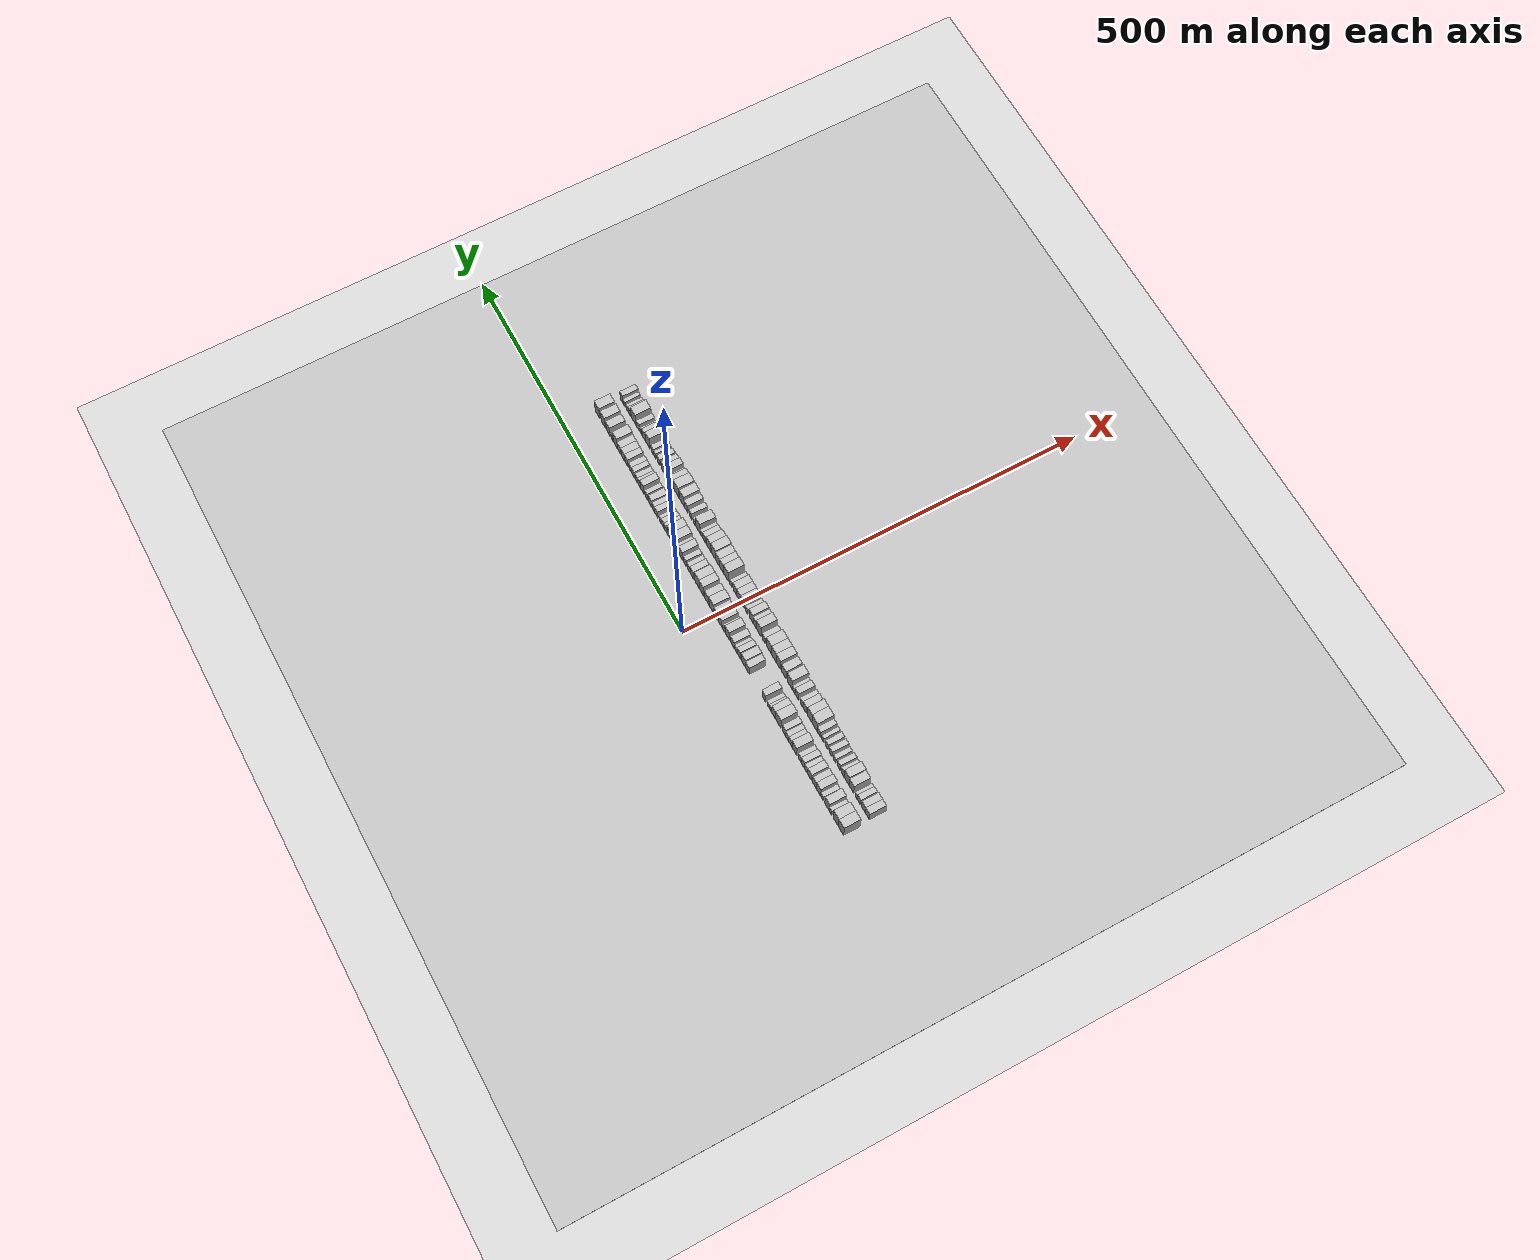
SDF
<?xml version="1.0" encoding="utf-8"?>

<sdf version="1.6">

   <world name="default">

      <gui fullscreen="0">

         <camera name="user_camera">

            <pose>-15 0 4.57585 0 0 0</pose>

            <view_controller>orbit</view_controller>

         </camera>

      </gui>

      <scene>

         <sky>

           <clouds>

             <speed>12</speed>

           </clouds>

         </sky>

         <ambient>0.4 0.4 0.4 1</ambient>

         <background>0.7 0.7 0.7 1</background>

         <shadows>1</shadows>

      </scene>

      <gravity>0 0 -9.8066</gravity>

      <magnetic_field>6e-06 2.3e-05 -4.2e-05</magnetic_field>

      <physics default="0" name="default_physics" type="ode">

         <ode>

            <solver>

               <type>quick</type>

               <iters>10</iters>

               <sor>1.0</sor>

               <use_dynamic_moi_rescaling>0</use_dynamic_moi_rescaling>

            </solver>

            <constraints>

               <cfm>0</cfm>

               <erp>0.2</erp>

               <contact_max_correcting_vel>100</contact_max_correcting_vel>

               <contact_surface_layer>0.001</contact_surface_layer>

            </constraints>

         </ode>

         <max_step_size>0.004</max_step_size>

         <real_time_factor>1</real_time_factor>

         <real_time_update_rate>250</real_time_update_rate>

      </physics>

      <light name="sun" type="directional">

         <cast_shadows>1</cast_shadows>

         <pose>0 0 10 0 0 0</pose>

         <diffuse>0.8 0.8 0.8 1</diffuse>

         <specular>0.2 0.2 0.2 1</specular>

         <attenuation>

            <range>1000</range>

            <constant>0.9</constant>

            <linear>0.01</linear>

            <quadratic>0.001</quadratic>

         </attenuation>

         <direction>-0.5 0.1 -0.9</direction>

      </light>

      <include>

         <name>ground_plane_1</name>

         <uri>model://HANNAS_ground_plane</uri>

         <pose>0 0 0  0 0 0</pose>

      </include>

      <include>

         <name>ground_plane_2</name>

         <uri>model://HANNAS_ground_plane</uri>

         <pose>100 0 0  0 0 0</pose>

      </include>

      <model name="building_1">

         <static>1</static>

         <pose frame="">50.0000 -278.4697 0 0.000000 0.000000 0.000000</pose>

         <link name="link">

            <pose frame="">0 0 12.00 0 0 0</pose>

            <collision name="collision">

               <geometry>

                  <box>

                     <size>20.0000 11.0606 24.0000</size>

                  </box>

               </geometry>

               <max_contacts>10</max_contacts>

               <surface>

                  <contact>

                     <ode/>

                  </contact>

                  <bounce/>

                  <friction>

                     <torsional>

                        <ode/>

                     </torsional>

                     <ode/>

                  </friction>

               </surface>

            </collision>

            <visual name="visual">

               <cast_shadows>0</cast_shadows>

               <geometry>

                  <box>

                     <size>20.0000 11.0606 24.0000</size>

                  </box>

               </geometry>

               <material>

                  <script>

                     <uri>model://HANNAS_wall/materials/scripts</uri>

                     <uri>model://HANNAS_wall/materials/textures</uri>

                     <name>vrc/HANNAS_wall</name>

                  </script>

               </material>

            </visual>

            <self_collide>0</self_collide>

            <enable_wind>0</enable_wind>

            <kinematic>0</kinematic>

         </link>

      </model>

      <model name="building_2">

         <static>1</static>

         <pose frame="">50.0000 -267.3348 0 0.000000 0.000000 0.000000</pose>

         <link name="link">

            <pose frame="">0 0 12.00 0 0 0</pose>

            <collision name="collision">

               <geometry>

                  <box>

                     <size>20.0000 11.2092 24.0000</size>

                  </box>

               </geometry>

               <max_contacts>10</max_contacts>

               <surface>

                  <contact>

                     <ode/>

                  </contact>

                  <bounce/>

                  <friction>

                     <torsional>

                        <ode/>

                     </torsional>

                     <ode/>

                  </friction>

               </surface>

            </collision>

            <visual name="visual">

               <cast_shadows>0</cast_shadows>

               <geometry>

                  <box>

                     <size>20.0000 11.2092 24.0000</size>

                  </box>

               </geometry>

               <material>

                  <script>

                     <uri>model://HANNAS_wall/materials/scripts</uri>

                     <uri>model://HANNAS_wall/materials/textures</uri>

                     <name>vrc/HANNAS_wall</name>

                  </script>

               </material>

            </visual>

            <self_collide>0</self_collide>

            <enable_wind>0</enable_wind>

            <kinematic>0</kinematic>

         </link>

      </model>

      <model name="building_3">

         <static>1</static>

         <pose frame="">50.0000 -256.1176 0 0.000000 0.000000 0.000000</pose>

         <link name="link">

            <pose frame="">0 0 6.00 0 0 0</pose>

            <collision name="collision">

               <geometry>

                  <box>

                     <size>20.0000 5.2254 12.0000</size>

                  </box>

               </geometry>

               <max_contacts>10</max_contacts>

               <surface>

                  <contact>

                     <ode/>

                  </contact>

                  <bounce/>

                  <friction>

                     <torsional>

                        <ode/>

                     </torsional>

                     <ode/>

                  </friction>

               </surface>

            </collision>

            <visual name="visual">

               <cast_shadows>0</cast_shadows>

               <geometry>

                  <box>

                     <size>20.0000 5.2254 12.0000</size>

                  </box>

               </geometry>

               <material>

                  <script>

                     <uri>model://HANNAS_wall/materials/scripts</uri>

                     <uri>model://HANNAS_wall/materials/textures</uri>

                     <name>vrc/HANNAS_wall</name>

                  </script>

               </material>

            </visual>

            <self_collide>0</self_collide>

            <enable_wind>0</enable_wind>

            <kinematic>0</kinematic>

         </link>

      </model>

      <model name="building_4">

         <static>1</static>

         <pose frame="">50.0000 -248.7218 0 0.000000 0.000000 0.000000</pose>

         <link name="link">

            <pose frame="">0 0 10.50 0 0 0</pose>

            <collision name="collision">

               <geometry>

                  <box>

                     <size>20.0000 9.5662 21.0000</size>

                  </box>

               </geometry>

               <max_contacts>10</max_contacts>

               <surface>

                  <contact>

                     <ode/>

                  </contact>

                  <bounce/>

                  <friction>

                     <torsional>

                        <ode/>

                     </torsional>

                     <ode/>

                  </friction>

               </surface>

            </collision>

            <visual name="visual">

               <cast_shadows>0</cast_shadows>

               <geometry>

                  <box>

                     <size>20.0000 9.5662 21.0000</size>

                  </box>

               </geometry>

               <material>

                  <script>

                     <uri>model://HANNAS_wall/materials/scripts</uri>

                     <uri>model://HANNAS_wall/materials/textures</uri>

                     <name>vrc/HANNAS_wall</name>

                  </script>

               </material>

            </visual>

            <self_collide>0</self_collide>

            <enable_wind>0</enable_wind>

            <kinematic>0</kinematic>

         </link>

      </model>

      <model name="building_5">

         <static>1</static>

         <pose frame="">50.0000 -238.0001 0 0.000000 0.000000 0.000000</pose>

         <link name="link">

            <pose frame="">0 0 6.00 0 0 0</pose>

            <collision name="collision">

               <geometry>

                  <box>

                     <size>20.0000 5.8772 12.0000</size>

                  </box>

               </geometry>

               <max_contacts>10</max_contacts>

               <surface>

                  <contact>

                     <ode/>

                  </contact>

                  <bounce/>

                  <friction>

                     <torsional>

                        <ode/>

                     </torsional>

                     <ode/>

                  </friction>

               </surface>

            </collision>

            <visual name="visual">

               <cast_shadows>0</cast_shadows>

               <geometry>

                  <box>

                     <size>20.0000 5.8772 12.0000</size>

                  </box>

               </geometry>

               <material>

                  <script>

                     <uri>model://HANNAS_wall/materials/scripts</uri>

                     <uri>model://HANNAS_wall/materials/textures</uri>

                     <name>vrc/HANNAS_wall</name>

                  </script>

               </material>

            </visual>

            <self_collide>0</self_collide>

            <enable_wind>0</enable_wind>

            <kinematic>0</kinematic>

         </link>

      </model>

      <model name="building_6">

         <static>1</static>

         <pose frame="">50.0000 -230.4664 0 0.000000 0.000000 0.000000</pose>

         <link name="link">

            <pose frame="">0 0 10.50 0 0 0</pose>

            <collision name="collision">

               <geometry>

                  <box>

                     <size>20.0000 9.1902 21.0000</size>

                  </box>

               </geometry>

               <max_contacts>10</max_contacts>

               <surface>

                  <contact>

                     <ode/>

                  </contact>

                  <bounce/>

                  <friction>

                     <torsional>

                        <ode/>

                     </torsional>

                     <ode/>

                  </friction>

               </surface>

            </collision>

            <visual name="visual">

               <cast_shadows>0</cast_shadows>

               <geometry>

                  <box>

                     <size>20.0000 9.1902 21.0000</size>

                  </box>

               </geometry>

               <material>

                  <script>

                     <uri>model://HANNAS_wall/materials/scripts</uri>

                     <uri>model://HANNAS_wall/materials/textures</uri>

                     <name>vrc/HANNAS_wall</name>

                  </script>

               </material>

            </visual>

            <self_collide>0</self_collide>

            <enable_wind>0</enable_wind>

            <kinematic>0</kinematic>

         </link>

      </model>

      <model name="building_7">

         <static>1</static>

         <pose frame="">50.0000 -221.8036 0 0.000000 0.000000 0.000000</pose>

         <link name="link">

            <pose frame="">0 0 9.00 0 0 0</pose>

            <collision name="collision">

               <geometry>

                  <box>

                     <size>20.0000 8.1353 18.0000</size>

                  </box>

               </geometry>

               <max_contacts>10</max_contacts>

               <surface>

                  <contact>

                     <ode/>

                  </contact>

                  <bounce/>

                  <friction>

                     <torsional>

                        <ode/>

                     </torsional>

                     <ode/>

                  </friction>

               </surface>

            </collision>

            <visual name="visual">

               <cast_shadows>0</cast_shadows>

               <geometry>

                  <box>

                     <size>20.0000 8.1353 18.0000</size>

                  </box>

               </geometry>

               <material>

                  <script>

                     <uri>model://HANNAS_wall/materials/scripts</uri>

                     <uri>model://HANNAS_wall/materials/textures</uri>

                     <name>vrc/HANNAS_wall</name>

                  </script>

               </material>

            </visual>

            <self_collide>0</self_collide>

            <enable_wind>0</enable_wind>

            <kinematic>0</kinematic>

         </link>

      </model>

      <model name="building_8">

         <static>1</static>

         <pose frame="">50.0000 -211.4116 0 0.000000 0.000000 0.000000</pose>

         <link name="link">

            <pose frame="">0 0 9.00 0 0 0</pose>

            <collision name="collision">

               <geometry>

                  <box>

                     <size>20.0000 8.6487 18.0000</size>

                  </box>

               </geometry>

               <max_contacts>10</max_contacts>

               <surface>

                  <contact>

                     <ode/>

                  </contact>

                  <bounce/>

                  <friction>

                     <torsional>

                        <ode/>

                     </torsional>

                     <ode/>

                  </friction>

               </surface>

            </collision>

            <visual name="visual">

               <cast_shadows>0</cast_shadows>

               <geometry>

                  <box>

                     <size>20.0000 8.6487 18.0000</size>

                  </box>

               </geometry>

               <material>

                  <script>

                     <uri>model://HANNAS_wall/materials/scripts</uri>

                     <uri>model://HANNAS_wall/materials/textures</uri>

                     <name>vrc/HANNAS_wall</name>

                  </script>

               </material>

            </visual>

            <self_collide>0</self_collide>

            <enable_wind>0</enable_wind>

            <kinematic>0</kinematic>

         </link>

      </model>

      <model name="building_9">

         <static>1</static>

         <pose frame="">50.0000 -203.8114 0 0.000000 0.000000 0.000000</pose>

         <link name="link">

            <pose frame="">0 0 7.50 0 0 0</pose>

            <collision name="collision">

               <geometry>

                  <box>

                     <size>20.0000 6.5516 15.0000</size>

                  </box>

               </geometry>

               <max_contacts>10</max_contacts>

               <surface>

                  <contact>

                     <ode/>

                  </contact>

                  <bounce/>

                  <friction>

                     <torsional>

                        <ode/>

                     </torsional>

                     <ode/>

                  </friction>

               </surface>

            </collision>

            <visual name="visual">

               <cast_shadows>0</cast_shadows>

               <geometry>

                  <box>

                     <size>20.0000 6.5516 15.0000</size>

                  </box>

               </geometry>

               <material>

                  <script>

                     <uri>model://HANNAS_wall/materials/scripts</uri>

                     <uri>model://HANNAS_wall/materials/textures</uri>

                     <name>vrc/HANNAS_wall</name>

                  </script>

               </material>

            </visual>

            <self_collide>0</self_collide>

            <enable_wind>0</enable_wind>

            <kinematic>0</kinematic>

         </link>

      </model>

      <model name="building_10">

         <static>1</static>

         <pose frame="">50.0000 -196.7801 0 0.000000 0.000000 0.000000</pose>

         <link name="link">

            <pose frame="">0 0 9.00 0 0 0</pose>

            <collision name="collision">

               <geometry>

                  <box>

                     <size>20.0000 7.5111 18.0000</size>

                  </box>

               </geometry>

               <max_contacts>10</max_contacts>

               <surface>

                  <contact>

                     <ode/>

                  </contact>

                  <bounce/>

                  <friction>

                     <torsional>

                        <ode/>

                     </torsional>

                     <ode/>

                  </friction>

               </surface>

            </collision>

            <visual name="visual">

               <cast_shadows>0</cast_shadows>

               <geometry>

                  <box>

                     <size>20.0000 7.5111 18.0000</size>

                  </box>

               </geometry>

               <material>

                  <script>

                     <uri>model://HANNAS_wall/materials/scripts</uri>

                     <uri>model://HANNAS_wall/materials/textures</uri>

                     <name>vrc/HANNAS_wall</name>

                  </script>

               </material>

            </visual>

            <self_collide>0</self_collide>

            <enable_wind>0</enable_wind>

            <kinematic>0</kinematic>

         </link>

      </model>

      <model name="building_11">

         <static>1</static>

         <pose frame="">50.0000 -189.6941 0 0.000000 0.000000 0.000000</pose>

         <link name="link">

            <pose frame="">0 0 7.50 0 0 0</pose>

            <collision name="collision">

               <geometry>

                  <box>

                     <size>20.0000 6.6609 15.0000</size>

                  </box>

               </geometry>

               <max_contacts>10</max_contacts>

               <surface>

                  <contact>

                     <ode/>

                  </contact>

                  <bounce/>

                  <friction>

                     <torsional>

                        <ode/>

                     </torsional>

                     <ode/>

                  </friction>

               </surface>

            </collision>

            <visual name="visual">

               <cast_shadows>0</cast_shadows>

               <geometry>

                  <box>

                     <size>20.0000 6.6609 15.0000</size>

                  </box>

               </geometry>

               <material>

                  <script>

                     <uri>model://HANNAS_wall/materials/scripts</uri>

                     <uri>model://HANNAS_wall/materials/textures</uri>

                     <name>vrc/HANNAS_wall</name>

                  </script>

               </material>

            </visual>

            <self_collide>0</self_collide>

            <enable_wind>0</enable_wind>

            <kinematic>0</kinematic>

         </link>

      </model>

      <model name="building_12">

         <static>1</static>

         <pose frame="">50.0000 -178.1327 0 0.000000 0.000000 0.000000</pose>

         <link name="link">

            <pose frame="">0 0 10.50 0 0 0</pose>

            <collision name="collision">

               <geometry>

                  <box>

                     <size>20.0000 10.4620 21.0000</size>

                  </box>

               </geometry>

               <max_contacts>10</max_contacts>

               <surface>

                  <contact>

                     <ode/>

                  </contact>

                  <bounce/>

                  <friction>

                     <torsional>

                        <ode/>

                     </torsional>

                     <ode/>

                  </friction>

               </surface>

            </collision>

            <visual name="visual">

               <cast_shadows>0</cast_shadows>

               <geometry>

                  <box>

                     <size>20.0000 10.4620 21.0000</size>

                  </box>

               </geometry>

               <material>

                  <script>

                     <uri>model://HANNAS_wall/materials/scripts</uri>

                     <uri>model://HANNAS_wall/materials/textures</uri>

                     <name>vrc/HANNAS_wall</name>

                  </script>

               </material>

            </visual>

            <self_collide>0</self_collide>

            <enable_wind>0</enable_wind>

            <kinematic>0</kinematic>

         </link>

      </model>

      <model name="building_13">

         <static>1</static>

         <pose frame="">50.0000 -169.3278 0 0.000000 0.000000 0.000000</pose>

         <link name="link">

            <pose frame="">0 0 7.50 0 0 0</pose>

            <collision name="collision">

               <geometry>

                  <box>

                     <size>20.0000 7.1477 15.0000</size>

                  </box>

               </geometry>

               <max_contacts>10</max_contacts>

               <surface>

                  <contact>

                     <ode/>

                  </contact>

                  <bounce/>

                  <friction>

                     <torsional>

                        <ode/>

                     </torsional>

                     <ode/>

                  </friction>

               </surface>

            </collision>

            <visual name="visual">

               <cast_shadows>0</cast_shadows>

               <geometry>

                  <box>

                     <size>20.0000 7.1477 15.0000</size>

                  </box>

               </geometry>

               <material>

                  <script>

                     <uri>model://HANNAS_wall/materials/scripts</uri>

                     <uri>model://HANNAS_wall/materials/textures</uri>

                     <name>vrc/HANNAS_wall</name>

                  </script>

               </material>

            </visual>

            <self_collide>0</self_collide>

            <enable_wind>0</enable_wind>

            <kinematic>0</kinematic>

         </link>

      </model>

      <model name="building_14">

         <static>1</static>

         <pose frame="">50.0000 -162.3910 0 0.000000 0.000000 0.000000</pose>

         <link name="link">

            <pose frame="">0 0 7.50 0 0 0</pose>

            <collision name="collision">

               <geometry>

                  <box>

                     <size>20.0000 6.7259 15.0000</size>

                  </box>

               </geometry>

               <max_contacts>10</max_contacts>

               <surface>

                  <contact>

                     <ode/>

                  </contact>

                  <bounce/>

                  <friction>

                     <torsional>

                        <ode/>

                     </torsional>

                     <ode/>

                  </friction>

               </surface>

            </collision>

            <visual name="visual">

               <cast_shadows>0</cast_shadows>

               <geometry>

                  <box>

                     <size>20.0000 6.7259 15.0000</size>

                  </box>

               </geometry>

               <material>

                  <script>

                     <uri>model://HANNAS_wall/materials/scripts</uri>

                     <uri>model://HANNAS_wall/materials/textures</uri>

                     <name>vrc/HANNAS_wall</name>

                  </script>

               </material>

            </visual>

            <self_collide>0</self_collide>

            <enable_wind>0</enable_wind>

            <kinematic>0</kinematic>

         </link>

      </model>

      <model name="building_15">

         <static>1</static>

         <pose frame="">50.0000 -155.2637 0 0.000000 0.000000 0.000000</pose>

         <link name="link">

            <pose frame="">0 0 9.00 0 0 0</pose>

            <collision name="collision">

               <geometry>

                  <box>

                     <size>20.0000 7.5286 18.0000</size>

                  </box>

               </geometry>

               <max_contacts>10</max_contacts>

               <surface>

                  <contact>

                     <ode/>

                  </contact>

                  <bounce/>

                  <friction>

                     <torsional>

                        <ode/>

                     </torsional>

                     <ode/>

                  </friction>

               </surface>

            </collision>

            <visual name="visual">

               <cast_shadows>0</cast_shadows>

               <geometry>

                  <box>

                     <size>20.0000 7.5286 18.0000</size>

                  </box>

               </geometry>

               <material>

                  <script>

                     <uri>model://HANNAS_wall/materials/scripts</uri>

                     <uri>model://HANNAS_wall/materials/textures</uri>

                     <name>vrc/HANNAS_wall</name>

                  </script>

               </material>

            </visual>

            <self_collide>0</self_collide>

            <enable_wind>0</enable_wind>

            <kinematic>0</kinematic>

         </link>

      </model>

      <model name="building_16">

         <static>1</static>

         <pose frame="">50.0000 -142.8023 0 0.000000 0.000000 0.000000</pose>

         <link name="link">

            <pose frame="">0 0 12.00 0 0 0</pose>

            <collision name="collision">

               <geometry>

                  <box>

                     <size>20.0000 11.3943 24.0000</size>

                  </box>

               </geometry>

               <max_contacts>10</max_contacts>

               <surface>

                  <contact>

                     <ode/>

                  </contact>

                  <bounce/>

                  <friction>

                     <torsional>

                        <ode/>

                     </torsional>

                     <ode/>

                  </friction>

               </surface>

            </collision>

            <visual name="visual">

               <cast_shadows>0</cast_shadows>

               <geometry>

                  <box>

                     <size>20.0000 11.3943 24.0000</size>

                  </box>

               </geometry>

               <material>

                  <script>

                     <uri>model://HANNAS_wall/materials/scripts</uri>

                     <uri>model://HANNAS_wall/materials/textures</uri>

                     <name>vrc/HANNAS_wall</name>

                  </script>

               </material>

            </visual>

            <self_collide>0</self_collide>

            <enable_wind>0</enable_wind>

            <kinematic>0</kinematic>

         </link>

      </model>

      <model name="building_17">

         <static>1</static>

         <pose frame="">50.0000 -132.8097 0 0.000000 0.000000 0.000000</pose>

         <link name="link">

            <pose frame="">0 0 10.50 0 0 0</pose>

            <collision name="collision">

               <geometry>

                  <box>

                     <size>20.0000 8.5907 21.0000</size>

                  </box>

               </geometry>

               <max_contacts>10</max_contacts>

               <surface>

                  <contact>

                     <ode/>

                  </contact>

                  <bounce/>

                  <friction>

                     <torsional>

                        <ode/>

                     </torsional>

                     <ode/>

                  </friction>

               </surface>

            </collision>

            <visual name="visual">

               <cast_shadows>0</cast_shadows>

               <geometry>

                  <box>

                     <size>20.0000 8.5907 21.0000</size>

                  </box>

               </geometry>

               <material>

                  <script>

                     <uri>model://HANNAS_wall/materials/scripts</uri>

                     <uri>model://HANNAS_wall/materials/textures</uri>

                     <name>vrc/HANNAS_wall</name>

                  </script>

               </material>

            </visual>

            <self_collide>0</self_collide>

            <enable_wind>0</enable_wind>

            <kinematic>0</kinematic>

         </link>

      </model>

      <model name="building_18">

         <static>1</static>

         <pose frame="">50.0000 -125.5334 0 0.000000 0.000000 0.000000</pose>

         <link name="link">

            <pose frame="">0 0 6.00 0 0 0</pose>

            <collision name="collision">

               <geometry>

                  <box>

                     <size>20.0000 5.9619 12.0000</size>

                  </box>

               </geometry>

               <max_contacts>10</max_contacts>

               <surface>

                  <contact>

                     <ode/>

                  </contact>

                  <bounce/>

                  <friction>

                     <torsional>

                        <ode/>

                     </torsional>

                     <ode/>

                  </friction>

               </surface>

            </collision>

            <visual name="visual">

               <cast_shadows>0</cast_shadows>

               <geometry>

                  <box>

                     <size>20.0000 5.9619 12.0000</size>

                  </box>

               </geometry>

               <material>

                  <script>

                     <uri>model://HANNAS_wall/materials/scripts</uri>

                     <uri>model://HANNAS_wall/materials/textures</uri>

                     <name>vrc/HANNAS_wall</name>

                  </script>

               </material>

            </visual>

            <self_collide>0</self_collide>

            <enable_wind>0</enable_wind>

            <kinematic>0</kinematic>

         </link>

      </model>

      <model name="building_19">

         <static>1</static>

         <pose frame="">50.0000 -120.1101 0 0.000000 0.000000 0.000000</pose>

         <link name="link">

            <pose frame="">0 0 6.00 0 0 0</pose>

            <collision name="collision">

               <geometry>

                  <box>

                     <size>20.0000 4.8848 12.0000</size>

                  </box>

               </geometry>

               <max_contacts>10</max_contacts>

               <surface>

                  <contact>

                     <ode/>

                  </contact>

                  <bounce/>

                  <friction>

                     <torsional>

                        <ode/>

                     </torsional>

                     <ode/>

                  </friction>

               </surface>

            </collision>

            <visual name="visual">

               <cast_shadows>0</cast_shadows>

               <geometry>

                  <box>

                     <size>20.0000 4.8848 12.0000</size>

                  </box>

               </geometry>

               <material>

                  <script>

                     <uri>model://HANNAS_wall/materials/scripts</uri>

                     <uri>model://HANNAS_wall/materials/textures</uri>

                     <name>vrc/HANNAS_wall</name>

                  </script>

               </material>

            </visual>

            <self_collide>0</self_collide>

            <enable_wind>0</enable_wind>

            <kinematic>0</kinematic>

         </link>

      </model>

      <model name="building_20">

         <static>1</static>

         <pose frame="">50.0000 -110.5472 0 0.000000 0.000000 0.000000</pose>

         <link name="link">

            <pose frame="">0 0 9.00 0 0 0</pose>

            <collision name="collision">

               <geometry>

                  <box>

                     <size>20.0000 8.2411 18.0000</size>

                  </box>

               </geometry>

               <max_contacts>10</max_contacts>

               <surface>

                  <contact>

                     <ode/>

                  </contact>

                  <bounce/>

                  <friction>

                     <torsional>

                        <ode/>

                     </torsional>

                     <ode/>

                  </friction>

               </surface>

            </collision>

            <visual name="visual">

               <cast_shadows>0</cast_shadows>

               <geometry>

                  <box>

                     <size>20.0000 8.2411 18.0000</size>

                  </box>

               </geometry>

               <material>

                  <script>

                     <uri>model://HANNAS_wall/materials/scripts</uri>

                     <uri>model://HANNAS_wall/materials/textures</uri>

                     <name>vrc/HANNAS_wall</name>

                  </script>

               </material>

            </visual>

            <self_collide>0</self_collide>

            <enable_wind>0</enable_wind>

            <kinematic>0</kinematic>

         </link>

      </model>

      <model name="building_21">

         <static>1</static>

         <pose frame="">50.0000 -73.9878 0 0.000000 0.000000 0.000000</pose>

         <link name="link">

            <pose frame="">0 0 9.00 0 0 0</pose>

            <collision name="collision">

               <geometry>

                  <box>

                     <size>20.0000 8.2926 18.0000</size>

                  </box>

               </geometry>

               <max_contacts>10</max_contacts>

               <surface>

                  <contact>

                     <ode/>

                  </contact>

                  <bounce/>

                  <friction>

                     <torsional>

                        <ode/>

                     </torsional>

                     <ode/>

                  </friction>

               </surface>

            </collision>

            <visual name="visual">

               <cast_shadows>0</cast_shadows>

               <geometry>

                  <box>

                     <size>20.0000 8.2926 18.0000</size>

                  </box>

               </geometry>

               <material>

                  <script>

                     <uri>model://HANNAS_wall/materials/scripts</uri>

                     <uri>model://HANNAS_wall/materials/textures</uri>

                     <name>vrc/HANNAS_wall</name>

                  </script>

               </material>

            </visual>

            <self_collide>0</self_collide>

            <enable_wind>0</enable_wind>

            <kinematic>0</kinematic>

         </link>

      </model>

      <model name="building_22">

         <static>1</static>

         <pose frame="">50.0000 -64.9480 0 0.000000 0.000000 0.000000</pose>

         <link name="link">

            <pose frame="">0 0 10.50 0 0 0</pose>

            <collision name="collision">

               <geometry>

                  <box>

                     <size>20.0000 9.7870 21.0000</size>

                  </box>

               </geometry>

               <max_contacts>10</max_contacts>

               <surface>

                  <contact>

                     <ode/>

                  </contact>

                  <bounce/>

                  <friction>

                     <torsional>

                        <ode/>

                     </torsional>

                     <ode/>

                  </friction>

               </surface>

            </collision>

            <visual name="visual">

               <cast_shadows>0</cast_shadows>

               <geometry>

                  <box>

                     <size>20.0000 9.7870 21.0000</size>

                  </box>

               </geometry>

               <material>

                  <script>

                     <uri>model://HANNAS_wall/materials/scripts</uri>

                     <uri>model://HANNAS_wall/materials/textures</uri>

                     <name>vrc/HANNAS_wall</name>

                  </script>

               </material>

            </visual>

            <self_collide>0</self_collide>

            <enable_wind>0</enable_wind>

            <kinematic>0</kinematic>

         </link>

      </model>

      <model name="building_23">

         <static>1</static>

         <pose frame="">50.0000 -54.3780 0 0.000000 0.000000 0.000000</pose>

         <link name="link">

            <pose frame="">0 0 9.00 0 0 0</pose>

            <collision name="collision">

               <geometry>

                  <box>

                     <size>20.0000 7.3532 18.0000</size>

                  </box>

               </geometry>

               <max_contacts>10</max_contacts>

               <surface>

                  <contact>

                     <ode/>

                  </contact>

                  <bounce/>

                  <friction>

                     <torsional>

                        <ode/>

                     </torsional>

                     <ode/>

                  </friction>

               </surface>

            </collision>

            <visual name="visual">

               <cast_shadows>0</cast_shadows>

               <geometry>

                  <box>

                     <size>20.0000 7.3532 18.0000</size>

                  </box>

               </geometry>

               <material>

                  <script>

                     <uri>model://HANNAS_wall/materials/scripts</uri>

                     <uri>model://HANNAS_wall/materials/textures</uri>

                     <name>vrc/HANNAS_wall</name>

                  </script>

               </material>

            </visual>

            <self_collide>0</self_collide>

            <enable_wind>0</enable_wind>

            <kinematic>0</kinematic>

         </link>

      </model>

      <model name="building_24">

         <static>1</static>

         <pose frame="">50.0000 -47.7225 0 0.000000 0.000000 0.000000</pose>

         <link name="link">

            <pose frame="">0 0 6.00 0 0 0</pose>

            <collision name="collision">

               <geometry>

                  <box>

                     <size>20.0000 5.9577 12.0000</size>

                  </box>

               </geometry>

               <max_contacts>10</max_contacts>

               <surface>

                  <contact>

                     <ode/>

                  </contact>

                  <bounce/>

                  <friction>

                     <torsional>

                        <ode/>

                     </torsional>

                     <ode/>

                  </friction>

               </surface>

            </collision>

            <visual name="visual">

               <cast_shadows>0</cast_shadows>

               <geometry>

                  <box>

                     <size>20.0000 5.9577 12.0000</size>

                  </box>

               </geometry>

               <material>

                  <script>

                     <uri>model://HANNAS_wall/materials/scripts</uri>

                     <uri>model://HANNAS_wall/materials/textures</uri>

                     <name>vrc/HANNAS_wall</name>

                  </script>

               </material>

            </visual>

            <self_collide>0</self_collide>

            <enable_wind>0</enable_wind>

            <kinematic>0</kinematic>

         </link>

      </model>

      <model name="building_25">

         <static>1</static>

         <pose frame="">50.0000 -40.4584 0 0.000000 0.000000 0.000000</pose>

         <link name="link">

            <pose frame="">0 0 9.00 0 0 0</pose>

            <collision name="collision">

               <geometry>

                  <box>

                     <size>20.0000 8.5706 18.0000</size>

                  </box>

               </geometry>

               <max_contacts>10</max_contacts>

               <surface>

                  <contact>

                     <ode/>

                  </contact>

                  <bounce/>

                  <friction>

                     <torsional>

                        <ode/>

                     </torsional>

                     <ode/>

                  </friction>

               </surface>

            </collision>

            <visual name="visual">

               <cast_shadows>0</cast_shadows>

               <geometry>

                  <box>

                     <size>20.0000 8.5706 18.0000</size>

                  </box>

               </geometry>

               <material>

                  <script>

                     <uri>model://HANNAS_wall/materials/scripts</uri>

                     <uri>model://HANNAS_wall/materials/textures</uri>

                     <name>vrc/HANNAS_wall</name>

                  </script>

               </material>

            </visual>

            <self_collide>0</self_collide>

            <enable_wind>0</enable_wind>

            <kinematic>0</kinematic>

         </link>

      </model>

      <model name="building_26">

         <static>1</static>

         <pose frame="">50.0000 -28.0884 0 0.000000 0.000000 0.000000</pose>

         <link name="link">

            <pose frame="">0 0 10.50 0 0 0</pose>

            <collision name="collision">

               <geometry>

                  <box>

                     <size>20.0000 10.1693 21.0000</size>

                  </box>

               </geometry>

               <max_contacts>10</max_contacts>

               <surface>

                  <contact>

                     <ode/>

                  </contact>

                  <bounce/>

                  <friction>

                     <torsional>

                        <ode/>

                     </torsional>

                     <ode/>

                  </friction>

               </surface>

            </collision>

            <visual name="visual">

               <cast_shadows>0</cast_shadows>

               <geometry>

                  <box>

                     <size>20.0000 10.1693 21.0000</size>

                  </box>

               </geometry>

               <material>

                  <script>

                     <uri>model://HANNAS_wall/materials/scripts</uri>

                     <uri>model://HANNAS_wall/materials/textures</uri>

                     <name>vrc/HANNAS_wall</name>

                  </script>

               </material>

            </visual>

            <self_collide>0</self_collide>

            <enable_wind>0</enable_wind>

            <kinematic>0</kinematic>

         </link>

      </model>

      <model name="building_27">

         <static>1</static>

         <pose frame="">50.0000 -20.3685 0 0.000000 0.000000 0.000000</pose>

         <link name="link">

            <pose frame="">0 0 6.00 0 0 0</pose>

            <collision name="collision">

               <geometry>

                  <box>

                     <size>20.0000 5.2705 12.0000</size>

                  </box>

               </geometry>

               <max_contacts>10</max_contacts>

               <surface>

                  <contact>

                     <ode/>

                  </contact>

                  <bounce/>

                  <friction>

                     <torsional>

                        <ode/>

                     </torsional>

                     <ode/>

                  </friction>

               </surface>

            </collision>

            <visual name="visual">

               <cast_shadows>0</cast_shadows>

               <geometry>

                  <box>

                     <size>20.0000 5.2705 12.0000</size>

                  </box>

               </geometry>

               <material>

                  <script>

                     <uri>model://HANNAS_wall/materials/scripts</uri>

                     <uri>model://HANNAS_wall/materials/textures</uri>

                     <name>vrc/HANNAS_wall</name>

                  </script>

               </material>

            </visual>

            <self_collide>0</self_collide>

            <enable_wind>0</enable_wind>

            <kinematic>0</kinematic>

         </link>

      </model>

      <model name="building_28">

         <static>1</static>

         <pose frame="">50.0000 -11.8762 0 0.000000 0.000000 0.000000</pose>

         <link name="link">

            <pose frame="">0 0 9.00 0 0 0</pose>

            <collision name="collision">

               <geometry>

                  <box>

                     <size>20.0000 7.7143 18.0000</size>

                  </box>

               </geometry>

               <max_contacts>10</max_contacts>

               <surface>

                  <contact>

                     <ode/>

                  </contact>

                  <bounce/>

                  <friction>

                     <torsional>

                        <ode/>

                     </torsional>

                     <ode/>

                  </friction>

               </surface>

            </collision>

            <visual name="visual">

               <cast_shadows>0</cast_shadows>

               <geometry>

                  <box>

                     <size>20.0000 7.7143 18.0000</size>

                  </box>

               </geometry>

               <material>

                  <script>

                     <uri>model://HANNAS_wall/materials/scripts</uri>

                     <uri>model://HANNAS_wall/materials/textures</uri>

                     <name>vrc/HANNAS_wall</name>

                  </script>

               </material>

            </visual>

            <self_collide>0</self_collide>

            <enable_wind>0</enable_wind>

            <kinematic>0</kinematic>

         </link>

      </model>

      <model name="building_29">

         <static>1</static>

         <pose frame="">50.0000 -1.8797 0 0.000000 0.000000 0.000000</pose>

         <link name="link">

            <pose frame="">0 0 9.00 0 0 0</pose>

            <collision name="collision">

               <geometry>

                  <box>

                     <size>20.0000 8.2786 18.0000</size>

                  </box>

               </geometry>

               <max_contacts>10</max_contacts>

               <surface>

                  <contact>

                     <ode/>

                  </contact>

                  <bounce/>

                  <friction>

                     <torsional>

                        <ode/>

                     </torsional>

                     <ode/>

                  </friction>

               </surface>

            </collision>

            <visual name="visual">

               <cast_shadows>0</cast_shadows>

               <geometry>

                  <box>

                     <size>20.0000 8.2786 18.0000</size>

                  </box>

               </geometry>

               <material>

                  <script>

                     <uri>model://HANNAS_wall/materials/scripts</uri>

                     <uri>model://HANNAS_wall/materials/textures</uri>

                     <name>vrc/HANNAS_wall</name>

                  </script>

               </material>

            </visual>

            <self_collide>0</self_collide>

            <enable_wind>0</enable_wind>

            <kinematic>0</kinematic>

         </link>

      </model>

      <model name="building_30">

         <static>1</static>

         <pose frame="">50.0000 7.9761 0 0.000000 0.000000 0.000000</pose>

         <link name="link">

            <pose frame="">0 0 12.00 0 0 0</pose>

            <collision name="collision">

               <geometry>

                  <box>

                     <size>20.0000 11.4330 24.0000</size>

                  </box>

               </geometry>

               <max_contacts>10</max_contacts>

               <surface>

                  <contact>

                     <ode/>

                  </contact>

                  <bounce/>

                  <friction>

                     <torsional>

                        <ode/>

                     </torsional>

                     <ode/>

                  </friction>

               </surface>

            </collision>

            <visual name="visual">

               <cast_shadows>0</cast_shadows>

               <geometry>

                  <box>

                     <size>20.0000 11.4330 24.0000</size>

                  </box>

               </geometry>

               <material>

                  <script>

                     <uri>model://HANNAS_wall/materials/scripts</uri>

                     <uri>model://HANNAS_wall/materials/textures</uri>

                     <name>vrc/HANNAS_wall</name>

                  </script>

               </material>

            </visual>

            <self_collide>0</self_collide>

            <enable_wind>0</enable_wind>

            <kinematic>0</kinematic>

         </link>

      </model>

      <model name="building_31">

         <static>1</static>

         <pose frame="">50.0000 18.6461 0 0.000000 0.000000 0.000000</pose>

         <link name="link">

            <pose frame="">0 0 10.50 0 0 0</pose>

            <collision name="collision">

               <geometry>

                  <box>

                     <size>20.0000 9.9068 21.0000</size>

                  </box>

               </geometry>

               <max_contacts>10</max_contacts>

               <surface>

                  <contact>

                     <ode/>

                  </contact>

                  <bounce/>

                  <friction>

                     <torsional>

                        <ode/>

                     </torsional>

                     <ode/>

                  </friction>

               </surface>

            </collision>

            <visual name="visual">

               <cast_shadows>0</cast_shadows>

               <geometry>

                  <box>

                     <size>20.0000 9.9068 21.0000</size>

                  </box>

               </geometry>

               <material>

                  <script>

                     <uri>model://HANNAS_wall/materials/scripts</uri>

                     <uri>model://HANNAS_wall/materials/textures</uri>

                     <name>vrc/HANNAS_wall</name>

                  </script>

               </material>

            </visual>

            <self_collide>0</self_collide>

            <enable_wind>0</enable_wind>

            <kinematic>0</kinematic>

         </link>

      </model>

      <model name="building_32">

         <static>1</static>

         <pose frame="">50.0000 31.4543 0 0.000000 0.000000 0.000000</pose>

         <link name="link">

            <pose frame="">0 0 12.00 0 0 0</pose>

            <collision name="collision">

               <geometry>

                  <box>

                     <size>20.0000 9.7096 24.0000</size>

                  </box>

               </geometry>

               <max_contacts>10</max_contacts>

               <surface>

                  <contact>

                     <ode/>

                  </contact>

                  <bounce/>

                  <friction>

                     <torsional>

                        <ode/>

                     </torsional>

                     <ode/>

                  </friction>

               </surface>

            </collision>

            <visual name="visual">

               <cast_shadows>0</cast_shadows>

               <geometry>

                  <box>

                     <size>20.0000 9.7096 24.0000</size>

                  </box>

               </geometry>

               <material>

                  <script>

                     <uri>model://HANNAS_wall/materials/scripts</uri>

                     <uri>model://HANNAS_wall/materials/textures</uri>

                     <name>vrc/HANNAS_wall</name>

                  </script>

               </material>

            </visual>

            <self_collide>0</self_collide>

            <enable_wind>0</enable_wind>

            <kinematic>0</kinematic>

         </link>

      </model>

      <model name="building_33">

         <static>1</static>

         <pose frame="">50.0000 41.5467 0 0.000000 0.000000 0.000000</pose>

         <link name="link">

            <pose frame="">0 0 12.00 0 0 0</pose>

            <collision name="collision">

               <geometry>

                  <box>

                     <size>20.0000 10.4753 24.0000</size>

                  </box>

               </geometry>

               <max_contacts>10</max_contacts>

               <surface>

                  <contact>

                     <ode/>

                  </contact>

                  <bounce/>

                  <friction>

                     <torsional>

                        <ode/>

                     </torsional>

                     <ode/>

                  </friction>

               </surface>

            </collision>

            <visual name="visual">

               <cast_shadows>0</cast_shadows>

               <geometry>

                  <box>

                     <size>20.0000 10.4753 24.0000</size>

                  </box>

               </geometry>

               <material>

                  <script>

                     <uri>model://HANNAS_wall/materials/scripts</uri>

                     <uri>model://HANNAS_wall/materials/textures</uri>

                     <name>vrc/HANNAS_wall</name>

                  </script>

               </material>

            </visual>

            <self_collide>0</self_collide>

            <enable_wind>0</enable_wind>

            <kinematic>0</kinematic>

         </link>

      </model>

      <model name="building_34">

         <static>1</static>

         <pose frame="">50.0000 53.7701 0 0.000000 0.000000 0.000000</pose>

         <link name="link">

            <pose frame="">0 0 9.00 0 0 0</pose>

            <collision name="collision">

               <geometry>

                  <box>

                     <size>20.0000 7.9716 18.0000</size>

                  </box>

               </geometry>

               <max_contacts>10</max_contacts>

               <surface>

                  <contact>

                     <ode/>

                  </contact>

                  <bounce/>

                  <friction>

                     <torsional>

                        <ode/>

                     </torsional>

                     <ode/>

                  </friction>

               </surface>

            </collision>

            <visual name="visual">

               <cast_shadows>0</cast_shadows>

               <geometry>

                  <box>

                     <size>20.0000 7.9716 18.0000</size>

                  </box>

               </geometry>

               <material>

                  <script>

                     <uri>model://HANNAS_wall/materials/scripts</uri>

                     <uri>model://HANNAS_wall/materials/textures</uri>

                     <name>vrc/HANNAS_wall</name>

                  </script>

               </material>

            </visual>

            <self_collide>0</self_collide>

            <enable_wind>0</enable_wind>

            <kinematic>0</kinematic>

         </link>

      </model>

      <model name="building_35">

         <static>1</static>

         <pose frame="">50.0000 61.3067 0 0.000000 0.000000 0.000000</pose>

         <link name="link">

            <pose frame="">0 0 7.50 0 0 0</pose>

            <collision name="collision">

               <geometry>

                  <box>

                     <size>20.0000 7.1015 15.0000</size>

                  </box>

               </geometry>

               <max_contacts>10</max_contacts>

               <surface>

                  <contact>

                     <ode/>

                  </contact>

                  <bounce/>

                  <friction>

                     <torsional>

                        <ode/>

                     </torsional>

                     <ode/>

                  </friction>

               </surface>

            </collision>

            <visual name="visual">

               <cast_shadows>0</cast_shadows>

               <geometry>

                  <box>

                     <size>20.0000 7.1015 15.0000</size>

                  </box>

               </geometry>

               <material>

                  <script>

                     <uri>model://HANNAS_wall/materials/scripts</uri>

                     <uri>model://HANNAS_wall/materials/textures</uri>

                     <name>vrc/HANNAS_wall</name>

                  </script>

               </material>

            </visual>

            <self_collide>0</self_collide>

            <enable_wind>0</enable_wind>

            <kinematic>0</kinematic>

         </link>

      </model>

      <model name="building_36">

         <static>1</static>

         <pose frame="">50.0000 70.0731 0 0.000000 0.000000 0.000000</pose>

         <link name="link">

            <pose frame="">0 0 7.50 0 0 0</pose>

            <collision name="collision">

               <geometry>

                  <box>

                     <size>20.0000 6.4313 15.0000</size>

                  </box>

               </geometry>

               <max_contacts>10</max_contacts>

               <surface>

                  <contact>

                     <ode/>

                  </contact>

                  <bounce/>

                  <friction>

                     <torsional>

                        <ode/>

                     </torsional>

                     <ode/>

                  </friction>

               </surface>

            </collision>

            <visual name="visual">

               <cast_shadows>0</cast_shadows>

               <geometry>

                  <box>

                     <size>20.0000 6.4313 15.0000</size>

                  </box>

               </geometry>

               <material>

                  <script>

                     <uri>model://HANNAS_wall/materials/scripts</uri>

                     <uri>model://HANNAS_wall/materials/textures</uri>

                     <name>vrc/HANNAS_wall</name>

                  </script>

               </material>

            </visual>

            <self_collide>0</self_collide>

            <enable_wind>0</enable_wind>

            <kinematic>0</kinematic>

         </link>

      </model>

      <model name="building_37">

         <static>1</static>

         <pose frame="">50.0000 79.7075 0 0.000000 0.000000 0.000000</pose>

         <link name="link">

            <pose frame="">0 0 10.50 0 0 0</pose>

            <collision name="collision">

               <geometry>

                  <box>

                     <size>20.0000 8.8375 21.0000</size>

                  </box>

               </geometry>

               <max_contacts>10</max_contacts>

               <surface>

                  <contact>

                     <ode/>

                  </contact>

                  <bounce/>

                  <friction>

                     <torsional>

                        <ode/>

                     </torsional>

                     <ode/>

                  </friction>

               </surface>

            </collision>

            <visual name="visual">

               <cast_shadows>0</cast_shadows>

               <geometry>

                  <box>

                     <size>20.0000 8.8375 21.0000</size>

                  </box>

               </geometry>

               <material>

                  <script>

                     <uri>model://HANNAS_wall/materials/scripts</uri>

                     <uri>model://HANNAS_wall/materials/textures</uri>

                     <name>vrc/HANNAS_wall</name>

                  </script>

               </material>

            </visual>

            <self_collide>0</self_collide>

            <enable_wind>0</enable_wind>

            <kinematic>0</kinematic>

         </link>

      </model>

      <model name="building_38">

         <static>1</static>

         <pose frame="">50.0000 87.2910 0 0.000000 0.000000 0.000000</pose>

         <link name="link">

            <pose frame="">0 0 7.50 0 0 0</pose>

            <collision name="collision">

               <geometry>

                  <box>

                     <size>20.0000 6.3293 15.0000</size>

                  </box>

               </geometry>

               <max_contacts>10</max_contacts>

               <surface>

                  <contact>

                     <ode/>

                  </contact>

                  <bounce/>

                  <friction>

                     <torsional>

                        <ode/>

                     </torsional>

                     <ode/>

                  </friction>

               </surface>

            </collision>

            <visual name="visual">

               <cast_shadows>0</cast_shadows>

               <geometry>

                  <box>

                     <size>20.0000 6.3293 15.0000</size>

                  </box>

               </geometry>

               <material>

                  <script>

                     <uri>model://HANNAS_wall/materials/scripts</uri>

                     <uri>model://HANNAS_wall/materials/textures</uri>

                     <name>vrc/HANNAS_wall</name>

                  </script>

               </material>

            </visual>

            <self_collide>0</self_collide>

            <enable_wind>0</enable_wind>

            <kinematic>0</kinematic>

         </link>

      </model>

      <model name="building_39">

         <static>1</static>

         <pose frame="">50.0000 95.7228 0 0.000000 0.000000 0.000000</pose>

         <link name="link">

            <pose frame="">0 0 12.00 0 0 0</pose>

            <collision name="collision">

               <geometry>

                  <box>

                     <size>20.0000 10.5344 24.0000</size>

                  </box>

               </geometry>

               <max_contacts>10</max_contacts>

               <surface>

                  <contact>

                     <ode/>

                  </contact>

                  <bounce/>

                  <friction>

                     <torsional>

                        <ode/>

                     </torsional>

                     <ode/>

                  </friction>

               </surface>

            </collision>

            <visual name="visual">

               <cast_shadows>0</cast_shadows>

               <geometry>

                  <box>

                     <size>20.0000 10.5344 24.0000</size>

                  </box>

               </geometry>

               <material>

                  <script>

                     <uri>model://HANNAS_wall/materials/scripts</uri>

                     <uri>model://HANNAS_wall/materials/textures</uri>

                     <name>vrc/HANNAS_wall</name>

                  </script>

               </material>

            </visual>

            <self_collide>0</self_collide>

            <enable_wind>0</enable_wind>

            <kinematic>0</kinematic>

         </link>

      </model>

      <model name="building_40">

         <static>1</static>

         <pose frame="">50.0000 106.0783 0 0.000000 0.000000 0.000000</pose>

         <link name="link">

            <pose frame="">0 0 12.00 0 0 0</pose>

            <collision name="collision">

               <geometry>

                  <box>

                     <size>20.0000 10.1767 24.0000</size>

                  </box>

               </geometry>

               <max_contacts>10</max_contacts>

               <surface>

                  <contact>

                     <ode/>

                  </contact>

                  <bounce/>

                  <friction>

                     <torsional>

                        <ode/>

                     </torsional>

                     <ode/>

                  </friction>

               </surface>

            </collision>

            <visual name="visual">

               <cast_shadows>0</cast_shadows>

               <geometry>

                  <box>

                     <size>20.0000 10.1767 24.0000</size>

                  </box>

               </geometry>

               <material>

                  <script>

                     <uri>model://HANNAS_wall/materials/scripts</uri>

                     <uri>model://HANNAS_wall/materials/textures</uri>

                     <name>vrc/HANNAS_wall</name>

                  </script>

               </material>

            </visual>

            <self_collide>0</self_collide>

            <enable_wind>0</enable_wind>

            <kinematic>0</kinematic>

         </link>

      </model>

      <model name="building_41">

         <static>1</static>

         <pose frame="">50.0000 116.3353 0 0.000000 0.000000 0.000000</pose>

         <link name="link">

            <pose frame="">0 0 7.50 0 0 0</pose>

            <collision name="collision">

               <geometry>

                  <box>

                     <size>20.0000 6.3371 15.0000</size>

                  </box>

               </geometry>

               <max_contacts>10</max_contacts>

               <surface>

                  <contact>

                     <ode/>

                  </contact>

                  <bounce/>

                  <friction>

                     <torsional>

                        <ode/>

                     </torsional>

                     <ode/>

                  </friction>

               </surface>

            </collision>

            <visual name="visual">

               <cast_shadows>0</cast_shadows>

               <geometry>

                  <box>

                     <size>20.0000 6.3371 15.0000</size>

                  </box>

               </geometry>

               <material>

                  <script>

                     <uri>model://HANNAS_wall/materials/scripts</uri>

                     <uri>model://HANNAS_wall/materials/textures</uri>

                     <name>vrc/HANNAS_wall</name>

                  </script>

               </material>

            </visual>

            <self_collide>0</self_collide>

            <enable_wind>0</enable_wind>

            <kinematic>0</kinematic>

         </link>

      </model>

      <model name="building_42">

         <static>1</static>

         <pose frame="">50.0000 122.5918 0 0.000000 0.000000 0.000000</pose>

         <link name="link">

            <pose frame="">0 0 7.50 0 0 0</pose>

            <collision name="collision">

               <geometry>

                  <box>

                     <size>20.0000 6.1759 15.0000</size>

                  </box>

               </geometry>

               <max_contacts>10</max_contacts>

               <surface>

                  <contact>

                     <ode/>

                  </contact>

                  <bounce/>

                  <friction>

                     <torsional>

                        <ode/>

                     </torsional>

                     <ode/>

                  </friction>

               </surface>

            </collision>

            <visual name="visual">

               <cast_shadows>0</cast_shadows>

               <geometry>

                  <box>

                     <size>20.0000 6.1759 15.0000</size>

                  </box>

               </geometry>

               <material>

                  <script>

                     <uri>model://HANNAS_wall/materials/scripts</uri>

                     <uri>model://HANNAS_wall/materials/textures</uri>

                     <name>vrc/HANNAS_wall</name>

                  </script>

               </material>

            </visual>

            <self_collide>0</self_collide>

            <enable_wind>0</enable_wind>

            <kinematic>0</kinematic>

         </link>

      </model>

      <model name="building_43">

         <static>1</static>

         <pose frame="">50.0000 128.5750 0 0.000000 0.000000 0.000000</pose>

         <link name="link">

            <pose frame="">0 0 6.00 0 0 0</pose>

            <collision name="collision">

               <geometry>

                  <box>

                     <size>20.0000 5.7906 12.0000</size>

                  </box>

               </geometry>

               <max_contacts>10</max_contacts>

               <surface>

                  <contact>

                     <ode/>

                  </contact>

                  <bounce/>

                  <friction>

                     <torsional>

                        <ode/>

                     </torsional>

                     <ode/>

                  </friction>

               </surface>

            </collision>

            <visual name="visual">

               <cast_shadows>0</cast_shadows>

               <geometry>

                  <box>

                     <size>20.0000 5.7906 12.0000</size>

                  </box>

               </geometry>

               <material>

                  <script>

                     <uri>model://HANNAS_wall/materials/scripts</uri>

                     <uri>model://HANNAS_wall/materials/textures</uri>

                     <name>vrc/HANNAS_wall</name>

                  </script>

               </material>

            </visual>

            <self_collide>0</self_collide>

            <enable_wind>0</enable_wind>

            <kinematic>0</kinematic>

         </link>

      </model>

      <model name="building_44">

         <static>1</static>

         <pose frame="">50.0000 138.1663 0 0.000000 0.000000 0.000000</pose>

         <link name="link">

            <pose frame="">0 0 7.50 0 0 0</pose>

            <collision name="collision">

               <geometry>

                  <box>

                     <size>20.0000 7.3919 15.0000</size>

                  </box>

               </geometry>

               <max_contacts>10</max_contacts>

               <surface>

                  <contact>

                     <ode/>

                  </contact>

                  <bounce/>

                  <friction>

                     <torsional>

                        <ode/>

                     </torsional>

                     <ode/>

                  </friction>

               </surface>

            </collision>

            <visual name="visual">

               <cast_shadows>0</cast_shadows>

               <geometry>

                  <box>

                     <size>20.0000 7.3919 15.0000</size>

                  </box>

               </geometry>

               <material>

                  <script>

                     <uri>model://HANNAS_wall/materials/scripts</uri>

                     <uri>model://HANNAS_wall/materials/textures</uri>

                     <name>vrc/HANNAS_wall</name>

                  </script>

               </material>

            </visual>

            <self_collide>0</self_collide>

            <enable_wind>0</enable_wind>

            <kinematic>0</kinematic>

         </link>

      </model>

      <model name="building_45">

         <static>1</static>

         <pose frame="">50.0000 144.9747 0 0.000000 0.000000 0.000000</pose>

         <link name="link">

            <pose frame="">0 0 7.50 0 0 0</pose>

            <collision name="collision">

               <geometry>

                  <box>

                     <size>20.0000 6.2251 15.0000</size>

                  </box>

               </geometry>

               <max_contacts>10</max_contacts>

               <surface>

                  <contact>

                     <ode/>

                  </contact>

                  <bounce/>

                  <friction>

                     <torsional>

                        <ode/>

                     </torsional>

                     <ode/>

                  </friction>

               </surface>

            </collision>

            <visual name="visual">

               <cast_shadows>0</cast_shadows>

               <geometry>

                  <box>

                     <size>20.0000 6.2251 15.0000</size>

                  </box>

               </geometry>

               <material>

                  <script>

                     <uri>model://HANNAS_wall/materials/scripts</uri>

                     <uri>model://HANNAS_wall/materials/textures</uri>

                     <name>vrc/HANNAS_wall</name>

                  </script>

               </material>

            </visual>

            <self_collide>0</self_collide>

            <enable_wind>0</enable_wind>

            <kinematic>0</kinematic>

         </link>

      </model>

      <model name="building_46">

         <static>1</static>

         <pose frame="">50.0000 152.2790 0 0.000000 0.000000 0.000000</pose>

         <link name="link">

            <pose frame="">0 0 9.00 0 0 0</pose>

            <collision name="collision">

               <geometry>

                  <box>

                     <size>20.0000 8.3834 18.0000</size>

                  </box>

               </geometry>

               <max_contacts>10</max_contacts>

               <surface>

                  <contact>

                     <ode/>

                  </contact>

                  <bounce/>

                  <friction>

                     <torsional>

                        <ode/>

                     </torsional>

                     <ode/>

                  </friction>

               </surface>

            </collision>

            <visual name="visual">

               <cast_shadows>0</cast_shadows>

               <geometry>

                  <box>

                     <size>20.0000 8.3834 18.0000</size>

                  </box>

               </geometry>

               <material>

                  <script>

                     <uri>model://HANNAS_wall/materials/scripts</uri>

                     <uri>model://HANNAS_wall/materials/textures</uri>

                     <name>vrc/HANNAS_wall</name>

                  </script>

               </material>

            </visual>

            <self_collide>0</self_collide>

            <enable_wind>0</enable_wind>

            <kinematic>0</kinematic>

         </link>

      </model>

      <model name="building_47">

         <static>1</static>

         <pose frame="">50.0000 162.5664 0 0.000000 0.000000 0.000000</pose>

         <link name="link">

            <pose frame="">0 0 7.50 0 0 0</pose>

            <collision name="collision">

               <geometry>

                  <box>

                     <size>20.0000 6.1914 15.0000</size>

                  </box>

               </geometry>

               <max_contacts>10</max_contacts>

               <surface>

                  <contact>

                     <ode/>

                  </contact>

                  <bounce/>

                  <friction>

                     <torsional>

                        <ode/>

                     </torsional>

                     <ode/>

                  </friction>

               </surface>

            </collision>

            <visual name="visual">

               <cast_shadows>0</cast_shadows>

               <geometry>

                  <box>

                     <size>20.0000 6.1914 15.0000</size>

                  </box>

               </geometry>

               <material>

                  <script>

                     <uri>model://HANNAS_wall/materials/scripts</uri>

                     <uri>model://HANNAS_wall/materials/textures</uri>

                     <name>vrc/HANNAS_wall</name>

                  </script>

               </material>

            </visual>

            <self_collide>0</self_collide>

            <enable_wind>0</enable_wind>

            <kinematic>0</kinematic>

         </link>

      </model>

      <model name="building_48">

         <static>1</static>

         <pose frame="">50.0000 172.0053 0 0.000000 0.000000 0.000000</pose>

         <link name="link">

            <pose frame="">0 0 10.50 0 0 0</pose>

            <collision name="collision">

               <geometry>

                  <box>

                     <size>20.0000 8.6865 21.0000</size>

                  </box>

               </geometry>

               <max_contacts>10</max_contacts>

               <surface>

                  <contact>

                     <ode/>

                  </contact>

                  <bounce/>

                  <friction>

                     <torsional>

                        <ode/>

                     </torsional>

                     <ode/>

                  </friction>

               </surface>

            </collision>

            <visual name="visual">

               <cast_shadows>0</cast_shadows>

               <geometry>

                  <box>

                     <size>20.0000 8.6865 21.0000</size>

                  </box>

               </geometry>

               <material>

                  <script>

                     <uri>model://HANNAS_wall/materials/scripts</uri>

                     <uri>model://HANNAS_wall/materials/textures</uri>

                     <name>vrc/HANNAS_wall</name>

                  </script>

               </material>

            </visual>

            <self_collide>0</self_collide>

            <enable_wind>0</enable_wind>

            <kinematic>0</kinematic>

         </link>

      </model>

      <model name="building_49">

         <static>1</static>

         <pose frame="">50.0000 179.5448 0 0.000000 0.000000 0.000000</pose>

         <link name="link">

            <pose frame="">0 0 7.50 0 0 0</pose>

            <collision name="collision">

               <geometry>

                  <box>

                     <size>20.0000 6.3926 15.0000</size>

                  </box>

               </geometry>

               <max_contacts>10</max_contacts>

               <surface>

                  <contact>

                     <ode/>

                  </contact>

                  <bounce/>

                  <friction>

                     <torsional>

                        <ode/>

                     </torsional>

                     <ode/>

                  </friction>

               </surface>

            </collision>

            <visual name="visual">

               <cast_shadows>0</cast_shadows>

               <geometry>

                  <box>

                     <size>20.0000 6.3926 15.0000</size>

                  </box>

               </geometry>

               <material>

                  <script>

                     <uri>model://HANNAS_wall/materials/scripts</uri>

                     <uri>model://HANNAS_wall/materials/textures</uri>

                     <name>vrc/HANNAS_wall</name>

                  </script>

               </material>

            </visual>

            <self_collide>0</self_collide>

            <enable_wind>0</enable_wind>

            <kinematic>0</kinematic>

         </link>

      </model>

      <model name="building_50">

         <static>1</static>

         <pose frame="">50.0000 185.8304 0 0.000000 0.000000 0.000000</pose>

         <link name="link">

            <pose frame="">0 0 7.50 0 0 0</pose>

            <collision name="collision">

               <geometry>

                  <box>

                     <size>20.0000 6.1786 15.0000</size>

                  </box>

               </geometry>

               <max_contacts>10</max_contacts>

               <surface>

                  <contact>

                     <ode/>

                  </contact>

                  <bounce/>

                  <friction>

                     <torsional>

                        <ode/>

                     </torsional>

                     <ode/>

                  </friction>

               </surface>

            </collision>

            <visual name="visual">

               <cast_shadows>0</cast_shadows>

               <geometry>

                  <box>

                     <size>20.0000 6.1786 15.0000</size>

                  </box>

               </geometry>

               <material>

                  <script>

                     <uri>model://HANNAS_wall/materials/scripts</uri>

                     <uri>model://HANNAS_wall/materials/textures</uri>

                     <name>vrc/HANNAS_wall</name>

                  </script>

               </material>

            </visual>

            <self_collide>0</self_collide>

            <enable_wind>0</enable_wind>

            <kinematic>0</kinematic>

         </link>

      </model>

      <model name="building_51">

         <static>1</static>

         <pose frame="">50.0000 194.2965 0 0.000000 0.000000 0.000000</pose>

         <link name="link">

            <pose frame="">0 0 7.50 0 0 0</pose>

            <collision name="collision">

               <geometry>

                  <box>

                     <size>20.0000 6.7537 15.0000</size>

                  </box>

               </geometry>

               <max_contacts>10</max_contacts>

               <surface>

                  <contact>

                     <ode/>

                  </contact>

                  <bounce/>

                  <friction>

                     <torsional>

                        <ode/>

                     </torsional>

                     <ode/>

                  </friction>

               </surface>

            </collision>

            <visual name="visual">

               <cast_shadows>0</cast_shadows>

               <geometry>

                  <box>

                     <size>20.0000 6.7537 15.0000</size>

                  </box>

               </geometry>

               <material>

                  <script>

                     <uri>model://HANNAS_wall/materials/scripts</uri>

                     <uri>model://HANNAS_wall/materials/textures</uri>

                     <name>vrc/HANNAS_wall</name>

                  </script>

               </material>

            </visual>

            <self_collide>0</self_collide>

            <enable_wind>0</enable_wind>

            <kinematic>0</kinematic>

         </link>

      </model>

      <model name="building_52">

         <static>1</static>

         <pose frame="">50.0000 201.0290 0 0.000000 0.000000 0.000000</pose>

         <link name="link">

            <pose frame="">0 0 7.50 0 0 0</pose>

            <collision name="collision">

               <geometry>

                  <box>

                     <size>20.0000 6.7113 15.0000</size>

                  </box>

               </geometry>

               <max_contacts>10</max_contacts>

               <surface>

                  <contact>

                     <ode/>

                  </contact>

                  <bounce/>

                  <friction>

                     <torsional>

                        <ode/>

                     </torsional>

                     <ode/>

                  </friction>

               </surface>

            </collision>

            <visual name="visual">

               <cast_shadows>0</cast_shadows>

               <geometry>

                  <box>

                     <size>20.0000 6.7113 15.0000</size>

                  </box>

               </geometry>

               <material>

                  <script>

                     <uri>model://HANNAS_wall/materials/scripts</uri>

                     <uri>model://HANNAS_wall/materials/textures</uri>

                     <name>vrc/HANNAS_wall</name>

                  </script>

               </material>

            </visual>

            <self_collide>0</self_collide>

            <enable_wind>0</enable_wind>

            <kinematic>0</kinematic>

         </link>

      </model>

      <model name="building_53">

         <static>1</static>

         <pose frame="">50.0000 210.4382 0 0.000000 0.000000 0.000000</pose>

         <link name="link">

            <pose frame="">0 0 9.00 0 0 0</pose>

            <collision name="collision">

               <geometry>

                  <box>

                     <size>20.0000 8.1071 18.0000</size>

                  </box>

               </geometry>

               <max_contacts>10</max_contacts>

               <surface>

                  <contact>

                     <ode/>

                  </contact>

                  <bounce/>

                  <friction>

                     <torsional>

                        <ode/>

                     </torsional>

                     <ode/>

                  </friction>

               </surface>

            </collision>

            <visual name="visual">

               <cast_shadows>0</cast_shadows>

               <geometry>

                  <box>

                     <size>20.0000 8.1071 18.0000</size>

                  </box>

               </geometry>

               <material>

                  <script>

                     <uri>model://HANNAS_wall/materials/scripts</uri>

                     <uri>model://HANNAS_wall/materials/textures</uri>

                     <name>vrc/HANNAS_wall</name>

                  </script>

               </material>

            </visual>

            <self_collide>0</self_collide>

            <enable_wind>0</enable_wind>

            <kinematic>0</kinematic>

         </link>

      </model>

      <model name="building_54">

         <static>1</static>

         <pose frame="">50.0000 218.9860 0 0.000000 0.000000 0.000000</pose>

         <link name="link">

            <pose frame="">0 0 9.00 0 0 0</pose>

            <collision name="collision">

               <geometry>

                  <box>

                     <size>20.0000 8.9886 18.0000</size>

                  </box>

               </geometry>

               <max_contacts>10</max_contacts>

               <surface>

                  <contact>

                     <ode/>

                  </contact>

                  <bounce/>

                  <friction>

                     <torsional>

                        <ode/>

                     </torsional>

                     <ode/>

                  </friction>

               </surface>

            </collision>

            <visual name="visual">

               <cast_shadows>0</cast_shadows>

               <geometry>

                  <box>

                     <size>20.0000 8.9886 18.0000</size>

                  </box>

               </geometry>

               <material>

                  <script>

                     <uri>model://HANNAS_wall/materials/scripts</uri>

                     <uri>model://HANNAS_wall/materials/textures</uri>

                     <name>vrc/HANNAS_wall</name>

                  </script>

               </material>

            </visual>

            <self_collide>0</self_collide>

            <enable_wind>0</enable_wind>

            <kinematic>0</kinematic>

         </link>

      </model>

      <model name="building_55">

         <static>1</static>

         <pose frame="">50.0000 227.9775 0 0.000000 0.000000 0.000000</pose>

         <link name="link">

            <pose frame="">0 0 9.00 0 0 0</pose>

            <collision name="collision">

               <geometry>

                  <box>

                     <size>20.0000 8.9945 18.0000</size>

                  </box>

               </geometry>

               <max_contacts>10</max_contacts>

               <surface>

                  <contact>

                     <ode/>

                  </contact>

                  <bounce/>

                  <friction>

                     <torsional>

                        <ode/>

                     </torsional>

                     <ode/>

                  </friction>

               </surface>

            </collision>

            <visual name="visual">

               <cast_shadows>0</cast_shadows>

               <geometry>

                  <box>

                     <size>20.0000 8.9945 18.0000</size>

                  </box>

               </geometry>

               <material>

                  <script>

                     <uri>model://HANNAS_wall/materials/scripts</uri>

                     <uri>model://HANNAS_wall/materials/textures</uri>

                     <name>vrc/HANNAS_wall</name>

                  </script>

               </material>

            </visual>

            <self_collide>0</self_collide>

            <enable_wind>0</enable_wind>

            <kinematic>0</kinematic>

         </link>

      </model>

      <model name="building_56">

         <static>1</static>

         <pose frame="">50.0000 237.9417 0 0.000000 0.000000 0.000000</pose>

         <link name="link">

            <pose frame="">0 0 12.00 0 0 0</pose>

            <collision name="collision">

               <geometry>

                  <box>

                     <size>20.0000 10.9339 24.0000</size>

                  </box>

               </geometry>

               <max_contacts>10</max_contacts>

               <surface>

                  <contact>

                     <ode/>

                  </contact>

                  <bounce/>

                  <friction>

                     <torsional>

                        <ode/>

                     </torsional>

                     <ode/>

                  </friction>

               </surface>

            </collision>

            <visual name="visual">

               <cast_shadows>0</cast_shadows>

               <geometry>

                  <box>

                     <size>20.0000 10.9339 24.0000</size>

                  </box>

               </geometry>

               <material>

                  <script>

                     <uri>model://HANNAS_wall/materials/scripts</uri>

                     <uri>model://HANNAS_wall/materials/textures</uri>

                     <name>vrc/HANNAS_wall</name>

                  </script>

               </material>

            </visual>

            <self_collide>0</self_collide>

            <enable_wind>0</enable_wind>

            <kinematic>0</kinematic>

         </link>

      </model>

      <model name="building_57">

         <static>1</static>

         <pose frame="">50.0000 245.8787 0 0.000000 0.000000 0.000000</pose>

         <link name="link">

            <pose frame="">0 0 6.00 0 0 0</pose>

            <collision name="collision">

               <geometry>

                  <box>

                     <size>20.0000 4.9400 12.0000</size>

                  </box>

               </geometry>

               <max_contacts>10</max_contacts>

               <surface>

                  <contact>

                     <ode/>

                  </contact>

                  <bounce/>

                  <friction>

                     <torsional>

                        <ode/>

                     </torsional>

                     <ode/>

                  </friction>

               </surface>

            </collision>

            <visual name="visual">

               <cast_shadows>0</cast_shadows>

               <geometry>

                  <box>

                     <size>20.0000 4.9400 12.0000</size>

                  </box>

               </geometry>

               <material>

                  <script>

                     <uri>model://HANNAS_wall/materials/scripts</uri>

                     <uri>model://HANNAS_wall/materials/textures</uri>

                     <name>vrc/HANNAS_wall</name>

                  </script>

               </material>

            </visual>

            <self_collide>0</self_collide>

            <enable_wind>0</enable_wind>

            <kinematic>0</kinematic>

         </link>

      </model>

      <model name="building_58">

         <static>1</static>

         <pose frame="">50.0000 255.4350 0 0.000000 0.000000 0.000000</pose>

         <link name="link">

            <pose frame="">0 0 10.50 0 0 0</pose>

            <collision name="collision">

               <geometry>

                  <box>

                     <size>20.0000 10.1725 21.0000</size>

                  </box>

               </geometry>

               <max_contacts>10</max_contacts>

               <surface>

                  <contact>

                     <ode/>

                  </contact>

                  <bounce/>

                  <friction>

                     <torsional>

                        <ode/>

                     </torsional>

                     <ode/>

                  </friction>

               </surface>

            </collision>

            <visual name="visual">

               <cast_shadows>0</cast_shadows>

               <geometry>

                  <box>

                     <size>20.0000 10.1725 21.0000</size>

                  </box>

               </geometry>

               <material>

                  <script>

                     <uri>model://HANNAS_wall/materials/scripts</uri>

                     <uri>model://HANNAS_wall/materials/textures</uri>

                     <name>vrc/HANNAS_wall</name>

                  </script>

               </material>

            </visual>

            <self_collide>0</self_collide>

            <enable_wind>0</enable_wind>

            <kinematic>0</kinematic>

         </link>

      </model>

      <model name="building_59">

         <static>1</static>

         <pose frame="">50.0000 267.9128 0 0.000000 0.000000 0.000000</pose>

         <link name="link">

            <pose frame="">0 0 12.00 0 0 0</pose>

            <collision name="collision">

               <geometry>

                  <box>

                     <size>20.0000 10.7831 24.0000</size>

                  </box>

               </geometry>

               <max_contacts>10</max_contacts>

               <surface>

                  <contact>

                     <ode/>

                  </contact>

                  <bounce/>

                  <friction>

                     <torsional>

                        <ode/>

                     </torsional>

                     <ode/>

                  </friction>

               </surface>

            </collision>

            <visual name="visual">

               <cast_shadows>0</cast_shadows>

               <geometry>

                  <box>

                     <size>20.0000 10.7831 24.0000</size>

                  </box>

               </geometry>

               <material>

                  <script>

                     <uri>model://HANNAS_wall/materials/scripts</uri>

                     <uri>model://HANNAS_wall/materials/textures</uri>

                     <name>vrc/HANNAS_wall</name>

                  </script>

               </material>

            </visual>

            <self_collide>0</self_collide>

            <enable_wind>0</enable_wind>

            <kinematic>0</kinematic>

         </link>

      </model>

      <model name="building_60">

         <static>1</static>

         <pose frame="">50.0000 282.1085 0 0.000000 0.000000 0.000000</pose>

         <link name="link">

            <pose frame="">0 0 12.00 0 0 0</pose>

            <collision name="collision">

               <geometry>

                  <box>

                     <size>20.0000 11.6082 24.0000</size>

                  </box>

               </geometry>

               <max_contacts>10</max_contacts>

               <surface>

                  <contact>

                     <ode/>

                  </contact>

                  <bounce/>

                  <friction>

                     <torsional>

                        <ode/>

                     </torsional>

                     <ode/>

                  </friction>

               </surface>

            </collision>

            <visual name="visual">

               <cast_shadows>0</cast_shadows>

               <geometry>

                  <box>

                     <size>20.0000 11.6082 24.0000</size>

                  </box>

               </geometry>

               <material>

                  <script>

                     <uri>model://HANNAS_wall/materials/scripts</uri>

                     <uri>model://HANNAS_wall/materials/textures</uri>

                     <name>vrc/HANNAS_wall</name>

                  </script>

               </material>

            </visual>

            <self_collide>0</self_collide>

            <enable_wind>0</enable_wind>

            <kinematic>0</kinematic>

         </link>

      </model>

      <model name="building_61">

         <static>1</static>

         <pose frame="">82.0000 -277.8554 0 0.000000 0.000000 0.000000</pose>

         <link name="link">

            <pose frame="">0 0 9.00 0 0 0</pose>

            <collision name="collision">

               <geometry>

                  <box>

                     <size>20.0000 8.2891 18.0000</size>

                  </box>

               </geometry>

               <max_contacts>10</max_contacts>

               <surface>

                  <contact>

                     <ode/>

                  </contact>

                  <bounce/>

                  <friction>

                     <torsional>

                        <ode/>

                     </torsional>

                     <ode/>

                  </friction>

               </surface>

            </collision>

            <visual name="visual">

               <cast_shadows>0</cast_shadows>

               <geometry>

                  <box>

                     <size>20.0000 8.2891 18.0000</size>

                  </box>

               </geometry>

               <material>

                  <script>

                     <uri>model://HANNAS_wall/materials/scripts</uri>

                     <uri>model://HANNAS_wall/materials/textures</uri>

                     <name>vrc/HANNAS_wall</name>

                  </script>

               </material>

            </visual>

            <self_collide>0</self_collide>

            <enable_wind>0</enable_wind>

            <kinematic>0</kinematic>

         </link>

      </model>

      <model name="building_62">

         <static>1</static>

         <pose frame="">82.0000 -269.5396 0 0.000000 0.000000 0.000000</pose>

         <link name="link">

            <pose frame="">0 0 9.00 0 0 0</pose>

            <collision name="collision">

               <geometry>

                  <box>

                     <size>20.0000 8.3425 18.0000</size>

                  </box>

               </geometry>

               <max_contacts>10</max_contacts>

               <surface>

                  <contact>

                     <ode/>

                  </contact>

                  <bounce/>

                  <friction>

                     <torsional>

                        <ode/>

                     </torsional>

                     <ode/>

                  </friction>

               </surface>

            </collision>

            <visual name="visual">

               <cast_shadows>0</cast_shadows>

               <geometry>

                  <box>

                     <size>20.0000 8.3425 18.0000</size>

                  </box>

               </geometry>

               <material>

                  <script>

                     <uri>model://HANNAS_wall/materials/scripts</uri>

                     <uri>model://HANNAS_wall/materials/textures</uri>

                     <name>vrc/HANNAS_wall</name>

                  </script>

               </material>

            </visual>

            <self_collide>0</self_collide>

            <enable_wind>0</enable_wind>

            <kinematic>0</kinematic>

         </link>

      </model>

      <model name="building_63">

         <static>1</static>

         <pose frame="">82.0000 -259.9513 0 0.000000 0.000000 0.000000</pose>

         <link name="link">

            <pose frame="">0 0 7.50 0 0 0</pose>

            <collision name="collision">

               <geometry>

                  <box>

                     <size>20.0000 6.8341 15.0000</size>

                  </box>

               </geometry>

               <max_contacts>10</max_contacts>

               <surface>

                  <contact>

                     <ode/>

                  </contact>

                  <bounce/>

                  <friction>

                     <torsional>

                        <ode/>

                     </torsional>

                     <ode/>

                  </friction>

               </surface>

            </collision>

            <visual name="visual">

               <cast_shadows>0</cast_shadows>

               <geometry>

                  <box>

                     <size>20.0000 6.8341 15.0000</size>

                  </box>

               </geometry>

               <material>

                  <script>

                     <uri>model://HANNAS_wall/materials/scripts</uri>

                     <uri>model://HANNAS_wall/materials/textures</uri>

                     <name>vrc/HANNAS_wall</name>

                  </script>

               </material>

            </visual>

            <self_collide>0</self_collide>

            <enable_wind>0</enable_wind>

            <kinematic>0</kinematic>

         </link>

      </model>

      <model name="building_64">

         <static>1</static>

         <pose frame="">82.0000 -254.0857 0 0.000000 0.000000 0.000000</pose>

         <link name="link">

            <pose frame="">0 0 6.00 0 0 0</pose>

            <collision name="collision">

               <geometry>

                  <box>

                     <size>20.0000 4.8971 12.0000</size>

                  </box>

               </geometry>

               <max_contacts>10</max_contacts>

               <surface>

                  <contact>

                     <ode/>

                  </contact>

                  <bounce/>

                  <friction>

                     <torsional>

                        <ode/>

                     </torsional>

                     <ode/>

                  </friction>

               </surface>

            </collision>

            <visual name="visual">

               <cast_shadows>0</cast_shadows>

               <geometry>

                  <box>

                     <size>20.0000 4.8971 12.0000</size>

                  </box>

               </geometry>

               <material>

                  <script>

                     <uri>model://HANNAS_wall/materials/scripts</uri>

                     <uri>model://HANNAS_wall/materials/textures</uri>

                     <name>vrc/HANNAS_wall</name>

                  </script>

               </material>

            </visual>

            <self_collide>0</self_collide>

            <enable_wind>0</enable_wind>

            <kinematic>0</kinematic>

         </link>

      </model>

      <model name="building_65">

         <static>1</static>

         <pose frame="">82.0000 -243.6845 0 0.000000 0.000000 0.000000</pose>

         <link name="link">

            <pose frame="">0 0 10.50 0 0 0</pose>

            <collision name="collision">

               <geometry>

                  <box>

                     <size>20.0000 9.9052 21.0000</size>

                  </box>

               </geometry>

               <max_contacts>10</max_contacts>

               <surface>

                  <contact>

                     <ode/>

                  </contact>

                  <bounce/>

                  <friction>

                     <torsional>

                        <ode/>

                     </torsional>

                     <ode/>

                  </friction>

               </surface>

            </collision>

            <visual name="visual">

               <cast_shadows>0</cast_shadows>

               <geometry>

                  <box>

                     <size>20.0000 9.9052 21.0000</size>

                  </box>

               </geometry>

               <material>

                  <script>

                     <uri>model://HANNAS_wall/materials/scripts</uri>

                     <uri>model://HANNAS_wall/materials/textures</uri>

                     <name>vrc/HANNAS_wall</name>

                  </script>

               </material>

            </visual>

            <self_collide>0</self_collide>

            <enable_wind>0</enable_wind>

            <kinematic>0</kinematic>

         </link>

      </model>

      <model name="building_66">

         <static>1</static>

         <pose frame="">82.0000 -233.7292 0 0.000000 0.000000 0.000000</pose>

         <link name="link">

            <pose frame="">0 0 12.00 0 0 0</pose>

            <collision name="collision">

               <geometry>

                  <box>

                     <size>20.0000 10.0055 24.0000</size>

                  </box>

               </geometry>

               <max_contacts>10</max_contacts>

               <surface>

                  <contact>

                     <ode/>

                  </contact>

                  <bounce/>

                  <friction>

                     <torsional>

                        <ode/>

                     </torsional>

                     <ode/>

                  </friction>

               </surface>

            </collision>

            <visual name="visual">

               <cast_shadows>0</cast_shadows>

               <geometry>

                  <box>

                     <size>20.0000 10.0055 24.0000</size>

                  </box>

               </geometry>

               <material>

                  <script>

                     <uri>model://HANNAS_wall/materials/scripts</uri>

                     <uri>model://HANNAS_wall/materials/textures</uri>

                     <name>vrc/HANNAS_wall</name>

                  </script>

               </material>

            </visual>

            <self_collide>0</self_collide>

            <enable_wind>0</enable_wind>

            <kinematic>0</kinematic>

         </link>

      </model>

      <model name="building_67">

         <static>1</static>

         <pose frame="">82.0000 -225.3629 0 0.000000 0.000000 0.000000</pose>

         <link name="link">

            <pose frame="">0 0 7.50 0 0 0</pose>

            <collision name="collision">

               <geometry>

                  <box>

                     <size>20.0000 6.7270 15.0000</size>

                  </box>

               </geometry>

               <max_contacts>10</max_contacts>

               <surface>

                  <contact>

                     <ode/>

                  </contact>

                  <bounce/>

                  <friction>

                     <torsional>

                        <ode/>

                     </torsional>

                     <ode/>

                  </friction>

               </surface>

            </collision>

            <visual name="visual">

               <cast_shadows>0</cast_shadows>

               <geometry>

                  <box>

                     <size>20.0000 6.7270 15.0000</size>

                  </box>

               </geometry>

               <material>

                  <script>

                     <uri>model://HANNAS_wall/materials/scripts</uri>

                     <uri>model://HANNAS_wall/materials/textures</uri>

                     <name>vrc/HANNAS_wall</name>

                  </script>

               </material>

            </visual>

            <self_collide>0</self_collide>

            <enable_wind>0</enable_wind>

            <kinematic>0</kinematic>

         </link>

      </model>

      <model name="building_68">

         <static>1</static>

         <pose frame="">82.0000 -216.8171 0 0.000000 0.000000 0.000000</pose>

         <link name="link">

            <pose frame="">0 0 7.50 0 0 0</pose>

            <collision name="collision">

               <geometry>

                  <box>

                     <size>20.0000 6.3647 15.0000</size>

                  </box>

               </geometry>

               <max_contacts>10</max_contacts>

               <surface>

                  <contact>

                     <ode/>

                  </contact>

                  <bounce/>

                  <friction>

                     <torsional>

                        <ode/>

                     </torsional>

                     <ode/>

                  </friction>

               </surface>

            </collision>

            <visual name="visual">

               <cast_shadows>0</cast_shadows>

               <geometry>

                  <box>

                     <size>20.0000 6.3647 15.0000</size>

                  </box>

               </geometry>

               <material>

                  <script>

                     <uri>model://HANNAS_wall/materials/scripts</uri>

                     <uri>model://HANNAS_wall/materials/textures</uri>

                     <name>vrc/HANNAS_wall</name>

                  </script>

               </material>

            </visual>

            <self_collide>0</self_collide>

            <enable_wind>0</enable_wind>

            <kinematic>0</kinematic>

         </link>

      </model>

      <model name="building_69">

         <static>1</static>

         <pose frame="">82.0000 -207.7804 0 0.000000 0.000000 0.000000</pose>

         <link name="link">

            <pose frame="">0 0 6.00 0 0 0</pose>

            <collision name="collision">

               <geometry>

                  <box>

                     <size>20.0000 5.7086 12.0000</size>

                  </box>

               </geometry>

               <max_contacts>10</max_contacts>

               <surface>

                  <contact>

                     <ode/>

                  </contact>

                  <bounce/>

                  <friction>

                     <torsional>

                        <ode/>

                     </torsional>

                     <ode/>

                  </friction>

               </surface>

            </collision>

            <visual name="visual">

               <cast_shadows>0</cast_shadows>

               <geometry>

                  <box>

                     <size>20.0000 5.7086 12.0000</size>

                  </box>

               </geometry>

               <material>

                  <script>

                     <uri>model://HANNAS_wall/materials/scripts</uri>

                     <uri>model://HANNAS_wall/materials/textures</uri>

                     <name>vrc/HANNAS_wall</name>

                  </script>

               </material>

            </visual>

            <self_collide>0</self_collide>

            <enable_wind>0</enable_wind>

            <kinematic>0</kinematic>

         </link>

      </model>

      <model name="building_70">

         <static>1</static>

         <pose frame="">82.0000 -199.4276 0 0.000000 0.000000 0.000000</pose>

         <link name="link">

            <pose frame="">0 0 7.50 0 0 0</pose>

            <collision name="collision">

               <geometry>

                  <box>

                     <size>20.0000 6.9970 15.0000</size>

                  </box>

               </geometry>

               <max_contacts>10</max_contacts>

               <surface>

                  <contact>

                     <ode/>

                  </contact>

                  <bounce/>

                  <friction>

                     <torsional>

                        <ode/>

                     </torsional>

                     <ode/>

                  </friction>

               </surface>

            </collision>

            <visual name="visual">

               <cast_shadows>0</cast_shadows>

               <geometry>

                  <box>

                     <size>20.0000 6.9970 15.0000</size>

                  </box>

               </geometry>

               <material>

                  <script>

                     <uri>model://HANNAS_wall/materials/scripts</uri>

                     <uri>model://HANNAS_wall/materials/textures</uri>

                     <name>vrc/HANNAS_wall</name>

                  </script>

               </material>

            </visual>

            <self_collide>0</self_collide>

            <enable_wind>0</enable_wind>

            <kinematic>0</kinematic>

         </link>

      </model>

      <model name="building_71">

         <static>1</static>

         <pose frame="">82.0000 -190.6926 0 0.000000 0.000000 0.000000</pose>

         <link name="link">

            <pose frame="">0 0 7.50 0 0 0</pose>

            <collision name="collision">

               <geometry>

                  <box>

                     <size>20.0000 6.4731 15.0000</size>

                  </box>

               </geometry>

               <max_contacts>10</max_contacts>

               <surface>

                  <contact>

                     <ode/>

                  </contact>

                  <bounce/>

                  <friction>

                     <torsional>

                        <ode/>

                     </torsional>

                     <ode/>

                  </friction>

               </surface>

            </collision>

            <visual name="visual">

               <cast_shadows>0</cast_shadows>

               <geometry>

                  <box>

                     <size>20.0000 6.4731 15.0000</size>

                  </box>

               </geometry>

               <material>

                  <script>

                     <uri>model://HANNAS_wall/materials/scripts</uri>

                     <uri>model://HANNAS_wall/materials/textures</uri>

                     <name>vrc/HANNAS_wall</name>

                  </script>

               </material>

            </visual>

            <self_collide>0</self_collide>

            <enable_wind>0</enable_wind>

            <kinematic>0</kinematic>

         </link>

      </model>

      <model name="building_72">

         <static>1</static>

         <pose frame="">82.0000 -182.0325 0 0.000000 0.000000 0.000000</pose>

         <link name="link">

            <pose frame="">0 0 6.00 0 0 0</pose>

            <collision name="collision">

               <geometry>

                  <box>

                     <size>20.0000 4.8470 12.0000</size>

                  </box>

               </geometry>

               <max_contacts>10</max_contacts>

               <surface>

                  <contact>

                     <ode/>

                  </contact>

                  <bounce/>

                  <friction>

                     <torsional>

                        <ode/>

                     </torsional>

                     <ode/>

                  </friction>

               </surface>

            </collision>

            <visual name="visual">

               <cast_shadows>0</cast_shadows>

               <geometry>

                  <box>

                     <size>20.0000 4.8470 12.0000</size>

                  </box>

               </geometry>

               <material>

                  <script>

                     <uri>model://HANNAS_wall/materials/scripts</uri>

                     <uri>model://HANNAS_wall/materials/textures</uri>

                     <name>vrc/HANNAS_wall</name>

                  </script>

               </material>

            </visual>

            <self_collide>0</self_collide>

            <enable_wind>0</enable_wind>

            <kinematic>0</kinematic>

         </link>

      </model>

      <model name="building_73">

         <static>1</static>

         <pose frame="">82.0000 -174.0696 0 0.000000 0.000000 0.000000</pose>

         <link name="link">

            <pose frame="">0 0 7.50 0 0 0</pose>

            <collision name="collision">

               <geometry>

                  <box>

                     <size>20.0000 7.0788 15.0000</size>

                  </box>

               </geometry>

               <max_contacts>10</max_contacts>

               <surface>

                  <contact>

                     <ode/>

                  </contact>

                  <bounce/>

                  <friction>

                     <torsional>

                        <ode/>

                     </torsional>

                     <ode/>

                  </friction>

               </surface>

            </collision>

            <visual name="visual">

               <cast_shadows>0</cast_shadows>

               <geometry>

                  <box>

                     <size>20.0000 7.0788 15.0000</size>

                  </box>

               </geometry>

               <material>

                  <script>

                     <uri>model://HANNAS_wall/materials/scripts</uri>

                     <uri>model://HANNAS_wall/materials/textures</uri>

                     <name>vrc/HANNAS_wall</name>

                  </script>

               </material>

            </visual>

            <self_collide>0</self_collide>

            <enable_wind>0</enable_wind>

            <kinematic>0</kinematic>

         </link>

      </model>

      <model name="building_74">

         <static>1</static>

         <pose frame="">82.0000 -164.5805 0 0.000000 0.000000 0.000000</pose>

         <link name="link">

            <pose frame="">0 0 12.00 0 0 0</pose>

            <collision name="collision">

               <geometry>

                  <box>

                     <size>20.0000 11.8994 24.0000</size>

                  </box>

               </geometry>

               <max_contacts>10</max_contacts>

               <surface>

                  <contact>

                     <ode/>

                  </contact>

                  <bounce/>

                  <friction>

                     <torsional>

                        <ode/>

                     </torsional>

                     <ode/>

                  </friction>

               </surface>

            </collision>

            <visual name="visual">

               <cast_shadows>0</cast_shadows>

               <geometry>

                  <box>

                     <size>20.0000 11.8994 24.0000</size>

                  </box>

               </geometry>

               <material>

                  <script>

                     <uri>model://HANNAS_wall/materials/scripts</uri>

                     <uri>model://HANNAS_wall/materials/textures</uri>

                     <name>vrc/HANNAS_wall</name>

                  </script>

               </material>

            </visual>

            <self_collide>0</self_collide>

            <enable_wind>0</enable_wind>

            <kinematic>0</kinematic>

         </link>

      </model>

      <model name="building_75">

         <static>1</static>

         <pose frame="">82.0000 -153.7266 0 0.000000 0.000000 0.000000</pose>

         <link name="link">

            <pose frame="">0 0 12.00 0 0 0</pose>

            <collision name="collision">

               <geometry>

                  <box>

                     <size>20.0000 9.8084 24.0000</size>

                  </box>

               </geometry>

               <max_contacts>10</max_contacts>

               <surface>

                  <contact>

                     <ode/>

                  </contact>

                  <bounce/>

                  <friction>

                     <torsional>

                        <ode/>

                     </torsional>

                     <ode/>

                  </friction>

               </surface>

            </collision>

            <visual name="visual">

               <cast_shadows>0</cast_shadows>

               <geometry>

                  <box>

                     <size>20.0000 9.8084 24.0000</size>

                  </box>

               </geometry>

               <material>

                  <script>

                     <uri>model://HANNAS_wall/materials/scripts</uri>

                     <uri>model://HANNAS_wall/materials/textures</uri>

                     <name>vrc/HANNAS_wall</name>

                  </script>

               </material>

            </visual>

            <self_collide>0</self_collide>

            <enable_wind>0</enable_wind>

            <kinematic>0</kinematic>

         </link>

      </model>

      <model name="building_76">

         <static>1</static>

         <pose frame="">82.0000 -142.8274 0 0.000000 0.000000 0.000000</pose>

         <link name="link">

            <pose frame="">0 0 9.00 0 0 0</pose>

            <collision name="collision">

               <geometry>

                  <box>

                     <size>20.0000 7.9900 18.0000</size>

                  </box>

               </geometry>

               <max_contacts>10</max_contacts>

               <surface>

                  <contact>

                     <ode/>

                  </contact>

                  <bounce/>

                  <friction>

                     <torsional>

                        <ode/>

                     </torsional>

                     <ode/>

                  </friction>

               </surface>

            </collision>

            <visual name="visual">

               <cast_shadows>0</cast_shadows>

               <geometry>

                  <box>

                     <size>20.0000 7.9900 18.0000</size>

                  </box>

               </geometry>

               <material>

                  <script>

                     <uri>model://HANNAS_wall/materials/scripts</uri>

                     <uri>model://HANNAS_wall/materials/textures</uri>

                     <name>vrc/HANNAS_wall</name>

                  </script>

               </material>

            </visual>

            <self_collide>0</self_collide>

            <enable_wind>0</enable_wind>

            <kinematic>0</kinematic>

         </link>

      </model>

      <model name="building_77">

         <static>1</static>

         <pose frame="">82.0000 -135.7622 0 0.000000 0.000000 0.000000</pose>

         <link name="link">

            <pose frame="">0 0 7.50 0 0 0</pose>

            <collision name="collision">

               <geometry>

                  <box>

                     <size>20.0000 6.1403 15.0000</size>

                  </box>

               </geometry>

               <max_contacts>10</max_contacts>

               <surface>

                  <contact>

                     <ode/>

                  </contact>

                  <bounce/>

                  <friction>

                     <torsional>

                        <ode/>

                     </torsional>

                     <ode/>

                  </friction>

               </surface>

            </collision>

            <visual name="visual">

               <cast_shadows>0</cast_shadows>

               <geometry>

                  <box>

                     <size>20.0000 6.1403 15.0000</size>

                  </box>

               </geometry>

               <material>

                  <script>

                     <uri>model://HANNAS_wall/materials/scripts</uri>

                     <uri>model://HANNAS_wall/materials/textures</uri>

                     <name>vrc/HANNAS_wall</name>

                  </script>

               </material>

            </visual>

            <self_collide>0</self_collide>

            <enable_wind>0</enable_wind>

            <kinematic>0</kinematic>

         </link>

      </model>

      <model name="building_78">

         <static>1</static>

         <pose frame="">82.0000 -125.5248 0 0.000000 0.000000 0.000000</pose>

         <link name="link">

            <pose frame="">0 0 9.00 0 0 0</pose>

            <collision name="collision">

               <geometry>

                  <box>

                     <size>20.0000 8.3344 18.0000</size>

                  </box>

               </geometry>

               <max_contacts>10</max_contacts>

               <surface>

                  <contact>

                     <ode/>

                  </contact>

                  <bounce/>

                  <friction>

                     <torsional>

                        <ode/>

                     </torsional>

                     <ode/>

                  </friction>

               </surface>

            </collision>

            <visual name="visual">

               <cast_shadows>0</cast_shadows>

               <geometry>

                  <box>

                     <size>20.0000 8.3344 18.0000</size>

                  </box>

               </geometry>

               <material>

                  <script>

                     <uri>model://HANNAS_wall/materials/scripts</uri>

                     <uri>model://HANNAS_wall/materials/textures</uri>

                     <name>vrc/HANNAS_wall</name>

                  </script>

               </material>

            </visual>

            <self_collide>0</self_collide>

            <enable_wind>0</enable_wind>

            <kinematic>0</kinematic>

         </link>

      </model>

      <model name="building_79">

         <static>1</static>

         <pose frame="">82.0000 -118.4855 0 0.000000 0.000000 0.000000</pose>

         <link name="link">

            <pose frame="">0 0 6.00 0 0 0</pose>

            <collision name="collision">

               <geometry>

                  <box>

                     <size>20.0000 5.7442 12.0000</size>

                  </box>

               </geometry>

               <max_contacts>10</max_contacts>

               <surface>

                  <contact>

                     <ode/>

                  </contact>

                  <bounce/>

                  <friction>

                     <torsional>

                        <ode/>

                     </torsional>

                     <ode/>

                  </friction>

               </surface>

            </collision>

            <visual name="visual">

               <cast_shadows>0</cast_shadows>

               <geometry>

                  <box>

                     <size>20.0000 5.7442 12.0000</size>

                  </box>

               </geometry>

               <material>

                  <script>

                     <uri>model://HANNAS_wall/materials/scripts</uri>

                     <uri>model://HANNAS_wall/materials/textures</uri>

                     <name>vrc/HANNAS_wall</name>

                  </script>

               </material>

            </visual>

            <self_collide>0</self_collide>

            <enable_wind>0</enable_wind>

            <kinematic>0</kinematic>

         </link>

      </model>

      <model name="building_80">

         <static>1</static>

         <pose frame="">82.0000 -110.1300 0 0.000000 0.000000 0.000000</pose>

         <link name="link">

            <pose frame="">0 0 12.00 0 0 0</pose>

            <collision name="collision">

               <geometry>

                  <box>

                     <size>20.0000 10.9669 24.0000</size>

                  </box>

               </geometry>

               <max_contacts>10</max_contacts>

               <surface>

                  <contact>

                     <ode/>

                  </contact>

                  <bounce/>

                  <friction>

                     <torsional>

                        <ode/>

                     </torsional>

                     <ode/>

                  </friction>

               </surface>

            </collision>

            <visual name="visual">

               <cast_shadows>0</cast_shadows>

               <geometry>

                  <box>

                     <size>20.0000 10.9669 24.0000</size>

                  </box>

               </geometry>

               <material>

                  <script>

                     <uri>model://HANNAS_wall/materials/scripts</uri>

                     <uri>model://HANNAS_wall/materials/textures</uri>

                     <name>vrc/HANNAS_wall</name>

                  </script>

               </material>

            </visual>

            <self_collide>0</self_collide>

            <enable_wind>0</enable_wind>

            <kinematic>0</kinematic>

         </link>

      </model>

      <model name="building_81">

         <static>1</static>

         <pose frame="">82.0000 -96.6548 0 0.000000 0.000000 0.000000</pose>

         <link name="link">

            <pose frame="">0 0 10.50 0 0 0</pose>

            <collision name="collision">

               <geometry>

                  <box>

                     <size>20.0000 9.9836 21.0000</size>

                  </box>

               </geometry>

               <max_contacts>10</max_contacts>

               <surface>

                  <contact>

                     <ode/>

                  </contact>

                  <bounce/>

                  <friction>

                     <torsional>

                        <ode/>

                     </torsional>

                     <ode/>

                  </friction>

               </surface>

            </collision>

            <visual name="visual">

               <cast_shadows>0</cast_shadows>

               <geometry>

                  <box>

                     <size>20.0000 9.9836 21.0000</size>

                  </box>

               </geometry>

               <material>

                  <script>

                     <uri>model://HANNAS_wall/materials/scripts</uri>

                     <uri>model://HANNAS_wall/materials/textures</uri>

                     <name>vrc/HANNAS_wall</name>

                  </script>

               </material>

            </visual>

            <self_collide>0</self_collide>

            <enable_wind>0</enable_wind>

            <kinematic>0</kinematic>

         </link>

      </model>

      <model name="building_82">

         <static>1</static>

         <pose frame="">82.0000 -84.5716 0 0.000000 0.000000 0.000000</pose>

         <link name="link">

            <pose frame="">0 0 12.00 0 0 0</pose>

            <collision name="collision">

               <geometry>

                  <box>

                     <size>20.0000 10.1828 24.0000</size>

                  </box>

               </geometry>

               <max_contacts>10</max_contacts>

               <surface>

                  <contact>

                     <ode/>

                  </contact>

                  <bounce/>

                  <friction>

                     <torsional>

                        <ode/>

                     </torsional>

                     <ode/>

                  </friction>

               </surface>

            </collision>

            <visual name="visual">

               <cast_shadows>0</cast_shadows>

               <geometry>

                  <box>

                     <size>20.0000 10.1828 24.0000</size>

                  </box>

               </geometry>

               <material>

                  <script>

                     <uri>model://HANNAS_wall/materials/scripts</uri>

                     <uri>model://HANNAS_wall/materials/textures</uri>

                     <name>vrc/HANNAS_wall</name>

                  </script>

               </material>

            </visual>

            <self_collide>0</self_collide>

            <enable_wind>0</enable_wind>

            <kinematic>0</kinematic>

         </link>

      </model>

      <model name="building_83">

         <static>1</static>

         <pose frame="">82.0000 -74.4212 0 0.000000 0.000000 0.000000</pose>

         <link name="link">

            <pose frame="">0 0 12.00 0 0 0</pose>

            <collision name="collision">

               <geometry>

                  <box>

                     <size>20.0000 10.1178 24.0000</size>

                  </box>

               </geometry>

               <max_contacts>10</max_contacts>

               <surface>

                  <contact>

                     <ode/>

                  </contact>

                  <bounce/>

                  <friction>

                     <torsional>

                        <ode/>

                     </torsional>

                     <ode/>

                  </friction>

               </surface>

            </collision>

            <visual name="visual">

               <cast_shadows>0</cast_shadows>

               <geometry>

                  <box>

                     <size>20.0000 10.1178 24.0000</size>

                  </box>

               </geometry>

               <material>

                  <script>

                     <uri>model://HANNAS_wall/materials/scripts</uri>

                     <uri>model://HANNAS_wall/materials/textures</uri>

                     <name>vrc/HANNAS_wall</name>

                  </script>

               </material>

            </visual>

            <self_collide>0</self_collide>

            <enable_wind>0</enable_wind>

            <kinematic>0</kinematic>

         </link>

      </model>

      <model name="building_84">

         <static>1</static>

         <pose frame="">82.0000 -63.6096 0 0.000000 0.000000 0.000000</pose>

         <link name="link">

            <pose frame="">0 0 12.00 0 0 0</pose>

            <collision name="collision">

               <geometry>

                  <box>

                     <size>20.0000 11.5054 24.0000</size>

                  </box>

               </geometry>

               <max_contacts>10</max_contacts>

               <surface>

                  <contact>

                     <ode/>

                  </contact>

                  <bounce/>

                  <friction>

                     <torsional>

                        <ode/>

                     </torsional>

                     <ode/>

                  </friction>

               </surface>

            </collision>

            <visual name="visual">

               <cast_shadows>0</cast_shadows>

               <geometry>

                  <box>

                     <size>20.0000 11.5054 24.0000</size>

                  </box>

               </geometry>

               <material>

                  <script>

                     <uri>model://HANNAS_wall/materials/scripts</uri>

                     <uri>model://HANNAS_wall/materials/textures</uri>

                     <name>vrc/HANNAS_wall</name>

                  </script>

               </material>

            </visual>

            <self_collide>0</self_collide>

            <enable_wind>0</enable_wind>

            <kinematic>0</kinematic>

         </link>

      </model>

      <model name="building_85">

         <static>1</static>

         <pose frame="">82.0000 -51.2688 0 0.000000 0.000000 0.000000</pose>

         <link name="link">

            <pose frame="">0 0 7.50 0 0 0</pose>

            <collision name="collision">

               <geometry>

                  <box>

                     <size>20.0000 7.1763 15.0000</size>

                  </box>

               </geometry>

               <max_contacts>10</max_contacts>

               <surface>

                  <contact>

                     <ode/>

                  </contact>

                  <bounce/>

                  <friction>

                     <torsional>

                        <ode/>

                     </torsional>

                     <ode/>

                  </friction>

               </surface>

            </collision>

            <visual name="visual">

               <cast_shadows>0</cast_shadows>

               <geometry>

                  <box>

                     <size>20.0000 7.1763 15.0000</size>

                  </box>

               </geometry>

               <material>

                  <script>

                     <uri>model://HANNAS_wall/materials/scripts</uri>

                     <uri>model://HANNAS_wall/materials/textures</uri>

                     <name>vrc/HANNAS_wall</name>

                  </script>

               </material>

            </visual>

            <self_collide>0</self_collide>

            <enable_wind>0</enable_wind>

            <kinematic>0</kinematic>

         </link>

      </model>

      <model name="building_86">

         <static>1</static>

         <pose frame="">82.0000 -40.4096 0 0.000000 0.000000 0.000000</pose>

         <link name="link">

            <pose frame="">0 0 12.00 0 0 0</pose>

            <collision name="collision">

               <geometry>

                  <box>

                     <size>20.0000 10.5422 24.0000</size>

                  </box>

               </geometry>

               <max_contacts>10</max_contacts>

               <surface>

                  <contact>

                     <ode/>

                  </contact>

                  <bounce/>

                  <friction>

                     <torsional>

                        <ode/>

                     </torsional>

                     <ode/>

                  </friction>

               </surface>

            </collision>

            <visual name="visual">

               <cast_shadows>0</cast_shadows>

               <geometry>

                  <box>

                     <size>20.0000 10.5422 24.0000</size>

                  </box>

               </geometry>

               <material>

                  <script>

                     <uri>model://HANNAS_wall/materials/scripts</uri>

                     <uri>model://HANNAS_wall/materials/textures</uri>

                     <name>vrc/HANNAS_wall</name>

                  </script>

               </material>

            </visual>

            <self_collide>0</self_collide>

            <enable_wind>0</enable_wind>

            <kinematic>0</kinematic>

         </link>

      </model>

      <model name="building_87">

         <static>1</static>

         <pose frame="">82.0000 -31.3382 0 0.000000 0.000000 0.000000</pose>

         <link name="link">

            <pose frame="">0 0 9.00 0 0 0</pose>

            <collision name="collision">

               <geometry>

                  <box>

                     <size>20.0000 7.6005 18.0000</size>

                  </box>

               </geometry>

               <max_contacts>10</max_contacts>

               <surface>

                  <contact>

                     <ode/>

                  </contact>

                  <bounce/>

                  <friction>

                     <torsional>

                        <ode/>

                     </torsional>

                     <ode/>

                  </friction>

               </surface>

            </collision>

            <visual name="visual">

               <cast_shadows>0</cast_shadows>

               <geometry>

                  <box>

                     <size>20.0000 7.6005 18.0000</size>

                  </box>

               </geometry>

               <material>

                  <script>

                     <uri>model://HANNAS_wall/materials/scripts</uri>

                     <uri>model://HANNAS_wall/materials/textures</uri>

                     <name>vrc/HANNAS_wall</name>

                  </script>

               </material>

            </visual>

            <self_collide>0</self_collide>

            <enable_wind>0</enable_wind>

            <kinematic>0</kinematic>

         </link>

      </model>

      <model name="building_88">

         <static>1</static>

         <pose frame="">82.0000 -22.9500 0 0.000000 0.000000 0.000000</pose>

         <link name="link">

            <pose frame="">0 0 10.50 0 0 0</pose>

            <collision name="collision">

               <geometry>

                  <box>

                     <size>20.0000 9.1758 21.0000</size>

                  </box>

               </geometry>

               <max_contacts>10</max_contacts>

               <surface>

                  <contact>

                     <ode/>

                  </contact>

                  <bounce/>

                  <friction>

                     <torsional>

                        <ode/>

                     </torsional>

                     <ode/>

                  </friction>

               </surface>

            </collision>

            <visual name="visual">

               <cast_shadows>0</cast_shadows>

               <geometry>

                  <box>

                     <size>20.0000 9.1758 21.0000</size>

                  </box>

               </geometry>

               <material>

                  <script>

                     <uri>model://HANNAS_wall/materials/scripts</uri>

                     <uri>model://HANNAS_wall/materials/textures</uri>

                     <name>vrc/HANNAS_wall</name>

                  </script>

               </material>

            </visual>

            <self_collide>0</self_collide>

            <enable_wind>0</enable_wind>

            <kinematic>0</kinematic>

         </link>

      </model>

      <model name="building_89">

         <static>1</static>

         <pose frame="">82.0000 -12.7396 0 0.000000 0.000000 0.000000</pose>

         <link name="link">

            <pose frame="">0 0 6.00 0 0 0</pose>

            <collision name="collision">

               <geometry>

                  <box>

                     <size>20.0000 5.2451 12.0000</size>

                  </box>

               </geometry>

               <max_contacts>10</max_contacts>

               <surface>

                  <contact>

                     <ode/>

                  </contact>

                  <bounce/>

                  <friction>

                     <torsional>

                        <ode/>

                     </torsional>

                     <ode/>

                  </friction>

               </surface>

            </collision>

            <visual name="visual">

               <cast_shadows>0</cast_shadows>

               <geometry>

                  <box>

                     <size>20.0000 5.2451 12.0000</size>

                  </box>

               </geometry>

               <material>

                  <script>

                     <uri>model://HANNAS_wall/materials/scripts</uri>

                     <uri>model://HANNAS_wall/materials/textures</uri>

                     <name>vrc/HANNAS_wall</name>

                  </script>

               </material>

            </visual>

            <self_collide>0</self_collide>

            <enable_wind>0</enable_wind>

            <kinematic>0</kinematic>

         </link>

      </model>

      <model name="building_90">

         <static>1</static>

         <pose frame="">82.0000 -3.6642 0 0.000000 0.000000 0.000000</pose>

         <link name="link">

            <pose frame="">0 0 9.00 0 0 0</pose>

            <collision name="collision">

               <geometry>

                  <box>

                     <size>20.0000 8.9056 18.0000</size>

                  </box>

               </geometry>

               <max_contacts>10</max_contacts>

               <surface>

                  <contact>

                     <ode/>

                  </contact>

                  <bounce/>

                  <friction>

                     <torsional>

                        <ode/>

                     </torsional>

                     <ode/>

                  </friction>

               </surface>

            </collision>

            <visual name="visual">

               <cast_shadows>0</cast_shadows>

               <geometry>

                  <box>

                     <size>20.0000 8.9056 18.0000</size>

                  </box>

               </geometry>

               <material>

                  <script>

                     <uri>model://HANNAS_wall/materials/scripts</uri>

                     <uri>model://HANNAS_wall/materials/textures</uri>

                     <name>vrc/HANNAS_wall</name>

                  </script>

               </material>

            </visual>

            <self_collide>0</self_collide>

            <enable_wind>0</enable_wind>

            <kinematic>0</kinematic>

         </link>

      </model>

      <model name="building_91">

         <static>1</static>

         <pose frame="">82.0000 5.1485 0 0.000000 0.000000 0.000000</pose>

         <link name="link">

            <pose frame="">0 0 9.00 0 0 0</pose>

            <collision name="collision">

               <geometry>

                  <box>

                     <size>20.0000 8.7198 18.0000</size>

                  </box>

               </geometry>

               <max_contacts>10</max_contacts>

               <surface>

                  <contact>

                     <ode/>

                  </contact>

                  <bounce/>

                  <friction>

                     <torsional>

                        <ode/>

                     </torsional>

                     <ode/>

                  </friction>

               </surface>

            </collision>

            <visual name="visual">

               <cast_shadows>0</cast_shadows>

               <geometry>

                  <box>

                     <size>20.0000 8.7198 18.0000</size>

                  </box>

               </geometry>

               <material>

                  <script>

                     <uri>model://HANNAS_wall/materials/scripts</uri>

                     <uri>model://HANNAS_wall/materials/textures</uri>

                     <name>vrc/HANNAS_wall</name>

                  </script>

               </material>

            </visual>

            <self_collide>0</self_collide>

            <enable_wind>0</enable_wind>

            <kinematic>0</kinematic>

         </link>

      </model>

      <model name="building_92">

         <static>1</static>

         <pose frame="">82.0000 13.9997 0 0.000000 0.000000 0.000000</pose>

         <link name="link">

            <pose frame="">0 0 9.00 0 0 0</pose>

            <collision name="collision">

               <geometry>

                  <box>

                     <size>20.0000 8.9825 18.0000</size>

                  </box>

               </geometry>

               <max_contacts>10</max_contacts>

               <surface>

                  <contact>

                     <ode/>

                  </contact>

                  <bounce/>

                  <friction>

                     <torsional>

                        <ode/>

                     </torsional>

                     <ode/>

                  </friction>

               </surface>

            </collision>

            <visual name="visual">

               <cast_shadows>0</cast_shadows>

               <geometry>

                  <box>

                     <size>20.0000 8.9825 18.0000</size>

                  </box>

               </geometry>

               <material>

                  <script>

                     <uri>model://HANNAS_wall/materials/scripts</uri>

                     <uri>model://HANNAS_wall/materials/textures</uri>

                     <name>vrc/HANNAS_wall</name>

                  </script>

               </material>

            </visual>

            <self_collide>0</self_collide>

            <enable_wind>0</enable_wind>

            <kinematic>0</kinematic>

         </link>

      </model>

      <model name="building_93">

         <static>1</static>

         <pose frame="">82.0000 23.0191 0 0.000000 0.000000 0.000000</pose>

         <link name="link">

            <pose frame="">0 0 6.00 0 0 0</pose>

            <collision name="collision">

               <geometry>

                  <box>

                     <size>20.0000 5.0563 12.0000</size>

                  </box>

               </geometry>

               <max_contacts>10</max_contacts>

               <surface>

                  <contact>

                     <ode/>

                  </contact>

                  <bounce/>

                  <friction>

                     <torsional>

                        <ode/>

                     </torsional>

                     <ode/>

                  </friction>

               </surface>

            </collision>

            <visual name="visual">

               <cast_shadows>0</cast_shadows>

               <geometry>

                  <box>

                     <size>20.0000 5.0563 12.0000</size>

                  </box>

               </geometry>

               <material>

                  <script>

                     <uri>model://HANNAS_wall/materials/scripts</uri>

                     <uri>model://HANNAS_wall/materials/textures</uri>

                     <name>vrc/HANNAS_wall</name>

                  </script>

               </material>

            </visual>

            <self_collide>0</self_collide>

            <enable_wind>0</enable_wind>

            <kinematic>0</kinematic>

         </link>

      </model>

      <model name="building_94">

         <static>1</static>

         <pose frame="">82.0000 34.1795 0 0.000000 0.000000 0.000000</pose>

         <link name="link">

            <pose frame="">0 0 12.00 0 0 0</pose>

            <collision name="collision">

               <geometry>

                  <box>

                     <size>20.0000 11.2644 24.0000</size>

                  </box>

               </geometry>

               <max_contacts>10</max_contacts>

               <surface>

                  <contact>

                     <ode/>

                  </contact>

                  <bounce/>

                  <friction>

                     <torsional>

                        <ode/>

                     </torsional>

                     <ode/>

                  </friction>

               </surface>

            </collision>

            <visual name="visual">

               <cast_shadows>0</cast_shadows>

               <geometry>

                  <box>

                     <size>20.0000 11.2644 24.0000</size>

                  </box>

               </geometry>

               <material>

                  <script>

                     <uri>model://HANNAS_wall/materials/scripts</uri>

                     <uri>model://HANNAS_wall/materials/textures</uri>

                     <name>vrc/HANNAS_wall</name>

                  </script>

               </material>

            </visual>

            <self_collide>0</self_collide>

            <enable_wind>0</enable_wind>

            <kinematic>0</kinematic>

         </link>

      </model>

      <model name="building_95">

         <static>1</static>

         <pose frame="">82.0000 44.3435 0 0.000000 0.000000 0.000000</pose>

         <link name="link">

            <pose frame="">0 0 10.50 0 0 0</pose>

            <collision name="collision">

               <geometry>

                  <box>

                     <size>20.0000 9.0637 21.0000</size>

                  </box>

               </geometry>

               <max_contacts>10</max_contacts>

               <surface>

                  <contact>

                     <ode/>

                  </contact>

                  <bounce/>

                  <friction>

                     <torsional>

                        <ode/>

                     </torsional>

                     <ode/>

                  </friction>

               </surface>

            </collision>

            <visual name="visual">

               <cast_shadows>0</cast_shadows>

               <geometry>

                  <box>

                     <size>20.0000 9.0637 21.0000</size>

                  </box>

               </geometry>

               <material>

                  <script>

                     <uri>model://HANNAS_wall/materials/scripts</uri>

                     <uri>model://HANNAS_wall/materials/textures</uri>

                     <name>vrc/HANNAS_wall</name>

                  </script>

               </material>

            </visual>

            <self_collide>0</self_collide>

            <enable_wind>0</enable_wind>

            <kinematic>0</kinematic>

         </link>

      </model>

      <model name="building_96">

         <static>1</static>

         <pose frame="">82.0000 53.5678 0 0.000000 0.000000 0.000000</pose>

         <link name="link">

            <pose frame="">0 0 10.50 0 0 0</pose>

            <collision name="collision">

               <geometry>

                  <box>

                     <size>20.0000 9.3848 21.0000</size>

                  </box>

               </geometry>

               <max_contacts>10</max_contacts>

               <surface>

                  <contact>

                     <ode/>

                  </contact>

                  <bounce/>

                  <friction>

                     <torsional>

                        <ode/>

                     </torsional>

                     <ode/>

                  </friction>

               </surface>

            </collision>

            <visual name="visual">

               <cast_shadows>0</cast_shadows>

               <geometry>

                  <box>

                     <size>20.0000 9.3848 21.0000</size>

                  </box>

               </geometry>

               <material>

                  <script>

                     <uri>model://HANNAS_wall/materials/scripts</uri>

                     <uri>model://HANNAS_wall/materials/textures</uri>

                     <name>vrc/HANNAS_wall</name>

                  </script>

               </material>

            </visual>

            <self_collide>0</self_collide>

            <enable_wind>0</enable_wind>

            <kinematic>0</kinematic>

         </link>

      </model>

      <model name="building_97">

         <static>1</static>

         <pose frame="">82.0000 63.7825 0 0.000000 0.000000 0.000000</pose>

         <link name="link">

            <pose frame="">0 0 12.00 0 0 0</pose>

            <collision name="collision">

               <geometry>

                  <box>

                     <size>20.0000 11.0447 24.0000</size>

                  </box>

               </geometry>

               <max_contacts>10</max_contacts>

               <surface>

                  <contact>

                     <ode/>

                  </contact>

                  <bounce/>

                  <friction>

                     <torsional>

                        <ode/>

                     </torsional>

                     <ode/>

                  </friction>

               </surface>

            </collision>

            <visual name="visual">

               <cast_shadows>0</cast_shadows>

               <geometry>

                  <box>

                     <size>20.0000 11.0447 24.0000</size>

                  </box>

               </geometry>

               <material>

                  <script>

                     <uri>model://HANNAS_wall/materials/scripts</uri>

                     <uri>model://HANNAS_wall/materials/textures</uri>

                     <name>vrc/HANNAS_wall</name>

                  </script>

               </material>

            </visual>

            <self_collide>0</self_collide>

            <enable_wind>0</enable_wind>

            <kinematic>0</kinematic>

         </link>

      </model>

      <model name="building_98">

         <static>1</static>

         <pose frame="">82.0000 74.5364 0 0.000000 0.000000 0.000000</pose>

         <link name="link">

            <pose frame="">0 0 10.50 0 0 0</pose>

            <collision name="collision">

               <geometry>

                  <box>

                     <size>20.0000 10.4630 21.0000</size>

                  </box>

               </geometry>

               <max_contacts>10</max_contacts>

               <surface>

                  <contact>

                     <ode/>

                  </contact>

                  <bounce/>

                  <friction>

                     <torsional>

                        <ode/>

                     </torsional>

                     <ode/>

                  </friction>

               </surface>

            </collision>

            <visual name="visual">

               <cast_shadows>0</cast_shadows>

               <geometry>

                  <box>

                     <size>20.0000 10.4630 21.0000</size>

                  </box>

               </geometry>

               <material>

                  <script>

                     <uri>model://HANNAS_wall/materials/scripts</uri>

                     <uri>model://HANNAS_wall/materials/textures</uri>

                     <name>vrc/HANNAS_wall</name>

                  </script>

               </material>

            </visual>

            <self_collide>0</self_collide>

            <enable_wind>0</enable_wind>

            <kinematic>0</kinematic>

         </link>

      </model>

      <model name="building_99">

         <static>1</static>

         <pose frame="">82.0000 85.5114 0 0.000000 0.000000 0.000000</pose>

         <link name="link">

            <pose frame="">0 0 7.50 0 0 0</pose>

            <collision name="collision">

               <geometry>

                  <box>

                     <size>20.0000 7.4872 15.0000</size>

                  </box>

               </geometry>

               <max_contacts>10</max_contacts>

               <surface>

                  <contact>

                     <ode/>

                  </contact>

                  <bounce/>

                  <friction>

                     <torsional>

                        <ode/>

                     </torsional>

                     <ode/>

                  </friction>

               </surface>

            </collision>

            <visual name="visual">

               <cast_shadows>0</cast_shadows>

               <geometry>

                  <box>

                     <size>20.0000 7.4872 15.0000</size>

                  </box>

               </geometry>

               <material>

                  <script>

                     <uri>model://HANNAS_wall/materials/scripts</uri>

                     <uri>model://HANNAS_wall/materials/textures</uri>

                     <name>vrc/HANNAS_wall</name>

                  </script>

               </material>

            </visual>

            <self_collide>0</self_collide>

            <enable_wind>0</enable_wind>

            <kinematic>0</kinematic>

         </link>

      </model>

      <model name="building_100">

         <static>1</static>

         <pose frame="">82.0000 91.9679 0 0.000000 0.000000 0.000000</pose>

         <link name="link">

            <pose frame="">0 0 6.00 0 0 0</pose>

            <collision name="collision">

               <geometry>

                  <box>

                     <size>20.0000 5.4258 12.0000</size>

                  </box>

               </geometry>

               <max_contacts>10</max_contacts>

               <surface>

                  <contact>

                     <ode/>

                  </contact>

                  <bounce/>

                  <friction>

                     <torsional>

                        <ode/>

                     </torsional>

                     <ode/>

                  </friction>

               </surface>

            </collision>

            <visual name="visual">

               <cast_shadows>0</cast_shadows>

               <geometry>

                  <box>

                     <size>20.0000 5.4258 12.0000</size>

                  </box>

               </geometry>

               <material>

                  <script>

                     <uri>model://HANNAS_wall/materials/scripts</uri>

                     <uri>model://HANNAS_wall/materials/textures</uri>

                     <name>vrc/HANNAS_wall</name>

                  </script>

               </material>

            </visual>

            <self_collide>0</self_collide>

            <enable_wind>0</enable_wind>

            <kinematic>0</kinematic>

         </link>

      </model>

      <model name="building_101">

         <static>1</static>

         <pose frame="">82.0000 100.3058 0 0.000000 0.000000 0.000000</pose>

         <link name="link">

            <pose frame="">0 0 12.00 0 0 0</pose>

            <collision name="collision">

               <geometry>

                  <box>

                     <size>20.0000 11.2501 24.0000</size>

                  </box>

               </geometry>

               <max_contacts>10</max_contacts>

               <surface>

                  <contact>

                     <ode/>

                  </contact>

                  <bounce/>

                  <friction>

                     <torsional>

                        <ode/>

                     </torsional>

                     <ode/>

                  </friction>

               </surface>

            </collision>

            <visual name="visual">

               <cast_shadows>0</cast_shadows>

               <geometry>

                  <box>

                     <size>20.0000 11.2501 24.0000</size>

                  </box>

               </geometry>

               <material>

                  <script>

                     <uri>model://HANNAS_wall/materials/scripts</uri>

                     <uri>model://HANNAS_wall/materials/textures</uri>

                     <name>vrc/HANNAS_wall</name>

                  </script>

               </material>

            </visual>

            <self_collide>0</self_collide>

            <enable_wind>0</enable_wind>

            <kinematic>0</kinematic>

         </link>

      </model>

      <model name="building_102">

         <static>1</static>

         <pose frame="">82.0000 108.5833 0 0.000000 0.000000 0.000000</pose>

         <link name="link">

            <pose frame="">0 0 6.00 0 0 0</pose>

            <collision name="collision">

               <geometry>

                  <box>

                     <size>20.0000 5.3048 12.0000</size>

                  </box>

               </geometry>

               <max_contacts>10</max_contacts>

               <surface>

                  <contact>

                     <ode/>

                  </contact>

                  <bounce/>

                  <friction>

                     <torsional>

                        <ode/>

                     </torsional>

                     <ode/>

                  </friction>

               </surface>

            </collision>

            <visual name="visual">

               <cast_shadows>0</cast_shadows>

               <geometry>

                  <box>

                     <size>20.0000 5.3048 12.0000</size>

                  </box>

               </geometry>

               <material>

                  <script>

                     <uri>model://HANNAS_wall/materials/scripts</uri>

                     <uri>model://HANNAS_wall/materials/textures</uri>

                     <name>vrc/HANNAS_wall</name>

                  </script>

               </material>

            </visual>

            <self_collide>0</self_collide>

            <enable_wind>0</enable_wind>

            <kinematic>0</kinematic>

         </link>

      </model>

      <model name="building_103">

         <static>1</static>

         <pose frame="">82.0000 117.5662 0 0.000000 0.000000 0.000000</pose>

         <link name="link">

            <pose frame="">0 0 7.50 0 0 0</pose>

            <collision name="collision">

               <geometry>

                  <box>

                     <size>20.0000 6.6611 15.0000</size>

                  </box>

               </geometry>

               <max_contacts>10</max_contacts>

               <surface>

                  <contact>

                     <ode/>

                  </contact>

                  <bounce/>

                  <friction>

                     <torsional>

                        <ode/>

                     </torsional>

                     <ode/>

                  </friction>

               </surface>

            </collision>

            <visual name="visual">

               <cast_shadows>0</cast_shadows>

               <geometry>

                  <box>

                     <size>20.0000 6.6611 15.0000</size>

                  </box>

               </geometry>

               <material>

                  <script>

                     <uri>model://HANNAS_wall/materials/scripts</uri>

                     <uri>model://HANNAS_wall/materials/textures</uri>

                     <name>vrc/HANNAS_wall</name>

                  </script>

               </material>

            </visual>

            <self_collide>0</self_collide>

            <enable_wind>0</enable_wind>

            <kinematic>0</kinematic>

         </link>

      </model>

      <model name="building_104">

         <static>1</static>

         <pose frame="">82.0000 128.1525 0 0.000000 0.000000 0.000000</pose>

         <link name="link">

            <pose frame="">0 0 9.00 0 0 0</pose>

            <collision name="collision">

               <geometry>

                  <box>

                     <size>20.0000 8.5114 18.0000</size>

                  </box>

               </geometry>

               <max_contacts>10</max_contacts>

               <surface>

                  <contact>

                     <ode/>

                  </contact>

                  <bounce/>

                  <friction>

                     <torsional>

                        <ode/>

                     </torsional>

                     <ode/>

                  </friction>

               </surface>

            </collision>

            <visual name="visual">

               <cast_shadows>0</cast_shadows>

               <geometry>

                  <box>

                     <size>20.0000 8.5114 18.0000</size>

                  </box>

               </geometry>

               <material>

                  <script>

                     <uri>model://HANNAS_wall/materials/scripts</uri>

                     <uri>model://HANNAS_wall/materials/textures</uri>

                     <name>vrc/HANNAS_wall</name>

                  </script>

               </material>

            </visual>

            <self_collide>0</self_collide>

            <enable_wind>0</enable_wind>

            <kinematic>0</kinematic>

         </link>

      </model>

      <model name="building_105">

         <static>1</static>

         <pose frame="">82.0000 137.8595 0 0.000000 0.000000 0.000000</pose>

         <link name="link">

            <pose frame="">0 0 12.00 0 0 0</pose>

            <collision name="collision">

               <geometry>

                  <box>

                     <size>20.0000 10.9026 24.0000</size>

                  </box>

               </geometry>

               <max_contacts>10</max_contacts>

               <surface>

                  <contact>

                     <ode/>

                  </contact>

                  <bounce/>

                  <friction>

                     <torsional>

                        <ode/>

                     </torsional>

                     <ode/>

                  </friction>

               </surface>

            </collision>

            <visual name="visual">

               <cast_shadows>0</cast_shadows>

               <geometry>

                  <box>

                     <size>20.0000 10.9026 24.0000</size>

                  </box>

               </geometry>

               <material>

                  <script>

                     <uri>model://HANNAS_wall/materials/scripts</uri>

                     <uri>model://HANNAS_wall/materials/textures</uri>

                     <name>vrc/HANNAS_wall</name>

                  </script>

               </material>

            </visual>

            <self_collide>0</self_collide>

            <enable_wind>0</enable_wind>

            <kinematic>0</kinematic>

         </link>

      </model>

      <model name="building_106">

         <static>1</static>

         <pose frame="">82.0000 151.2969 0 0.000000 0.000000 0.000000</pose>

         <link name="link">

            <pose frame="">0 0 12.00 0 0 0</pose>

            <collision name="collision">

               <geometry>

                  <box>

                     <size>20.0000 11.9722 24.0000</size>

                  </box>

               </geometry>

               <max_contacts>10</max_contacts>

               <surface>

                  <contact>

                     <ode/>

                  </contact>

                  <bounce/>

                  <friction>

                     <torsional>

                        <ode/>

                     </torsional>

                     <ode/>

                  </friction>

               </surface>

            </collision>

            <visual name="visual">

               <cast_shadows>0</cast_shadows>

               <geometry>

                  <box>

                     <size>20.0000 11.9722 24.0000</size>

                  </box>

               </geometry>

               <material>

                  <script>

                     <uri>model://HANNAS_wall/materials/scripts</uri>

                     <uri>model://HANNAS_wall/materials/textures</uri>

                     <name>vrc/HANNAS_wall</name>

                  </script>

               </material>

            </visual>

            <self_collide>0</self_collide>

            <enable_wind>0</enable_wind>

            <kinematic>0</kinematic>

         </link>

      </model>

      <model name="building_107">

         <static>1</static>

         <pose frame="">82.0000 161.4919 0 0.000000 0.000000 0.000000</pose>

         <link name="link">

            <pose frame="">0 0 10.50 0 0 0</pose>

            <collision name="collision">

               <geometry>

                  <box>

                     <size>20.0000 8.4177 21.0000</size>

                  </box>

               </geometry>

               <max_contacts>10</max_contacts>

               <surface>

                  <contact>

                     <ode/>

                  </contact>

                  <bounce/>

                  <friction>

                     <torsional>

                        <ode/>

                     </torsional>

                     <ode/>

                  </friction>

               </surface>

            </collision>

            <visual name="visual">

               <cast_shadows>0</cast_shadows>

               <geometry>

                  <box>

                     <size>20.0000 8.4177 21.0000</size>

                  </box>

               </geometry>

               <material>

                  <script>

                     <uri>model://HANNAS_wall/materials/scripts</uri>

                     <uri>model://HANNAS_wall/materials/textures</uri>

                     <name>vrc/HANNAS_wall</name>

                  </script>

               </material>

            </visual>

            <self_collide>0</self_collide>

            <enable_wind>0</enable_wind>

            <kinematic>0</kinematic>

         </link>

      </model>

      <model name="building_108">

         <static>1</static>

         <pose frame="">82.0000 168.6407 0 0.000000 0.000000 0.000000</pose>

         <link name="link">

            <pose frame="">0 0 6.00 0 0 0</pose>

            <collision name="collision">

               <geometry>

                  <box>

                     <size>20.0000 5.8800 12.0000</size>

                  </box>

               </geometry>

               <max_contacts>10</max_contacts>

               <surface>

                  <contact>

                     <ode/>

                  </contact>

                  <bounce/>

                  <friction>

                     <torsional>

                        <ode/>

                     </torsional>

                     <ode/>

                  </friction>

               </surface>

            </collision>

            <visual name="visual">

               <cast_shadows>0</cast_shadows>

               <geometry>

                  <box>

                     <size>20.0000 5.8800 12.0000</size>

                  </box>

               </geometry>

               <material>

                  <script>

                     <uri>model://HANNAS_wall/materials/scripts</uri>

                     <uri>model://HANNAS_wall/materials/textures</uri>

                     <name>vrc/HANNAS_wall</name>

                  </script>

               </material>

            </visual>

            <self_collide>0</self_collide>

            <enable_wind>0</enable_wind>

            <kinematic>0</kinematic>

         </link>

      </model>

      <model name="building_109">

         <static>1</static>

         <pose frame="">82.0000 175.8498 0 0.000000 0.000000 0.000000</pose>

         <link name="link">

            <pose frame="">0 0 10.50 0 0 0</pose>

            <collision name="collision">

               <geometry>

                  <box>

                     <size>20.0000 8.5383 21.0000</size>

                  </box>

               </geometry>

               <max_contacts>10</max_contacts>

               <surface>

                  <contact>

                     <ode/>

                  </contact>

                  <bounce/>

                  <friction>

                     <torsional>

                        <ode/>

                     </torsional>

                     <ode/>

                  </friction>

               </surface>

            </collision>

            <visual name="visual">

               <cast_shadows>0</cast_shadows>

               <geometry>

                  <box>

                     <size>20.0000 8.5383 21.0000</size>

                  </box>

               </geometry>

               <material>

                  <script>

                     <uri>model://HANNAS_wall/materials/scripts</uri>

                     <uri>model://HANNAS_wall/materials/textures</uri>

                     <name>vrc/HANNAS_wall</name>

                  </script>

               </material>

            </visual>

            <self_collide>0</self_collide>

            <enable_wind>0</enable_wind>

            <kinematic>0</kinematic>

         </link>

      </model>

      <model name="building_110">

         <static>1</static>

         <pose frame="">82.0000 183.9317 0 0.000000 0.000000 0.000000</pose>

         <link name="link">

            <pose frame="">0 0 9.00 0 0 0</pose>

            <collision name="collision">

               <geometry>

                  <box>

                     <size>20.0000 7.6254 18.0000</size>

                  </box>

               </geometry>

               <max_contacts>10</max_contacts>

               <surface>

                  <contact>

                     <ode/>

                  </contact>

                  <bounce/>

                  <friction>

                     <torsional>

                        <ode/>

                     </torsional>

                     <ode/>

                  </friction>

               </surface>

            </collision>

            <visual name="visual">

               <cast_shadows>0</cast_shadows>

               <geometry>

                  <box>

                     <size>20.0000 7.6254 18.0000</size>

                  </box>

               </geometry>

               <material>

                  <script>

                     <uri>model://HANNAS_wall/materials/scripts</uri>

                     <uri>model://HANNAS_wall/materials/textures</uri>

                     <name>vrc/HANNAS_wall</name>

                  </script>

               </material>

            </visual>

            <self_collide>0</self_collide>

            <enable_wind>0</enable_wind>

            <kinematic>0</kinematic>

         </link>

      </model>

      <model name="building_111">

         <static>1</static>

         <pose frame="">82.0000 194.2842 0 0.000000 0.000000 0.000000</pose>

         <link name="link">

            <pose frame="">0 0 7.50 0 0 0</pose>

            <collision name="collision">

               <geometry>

                  <box>

                     <size>20.0000 7.0797 15.0000</size>

                  </box>

               </geometry>

               <max_contacts>10</max_contacts>

               <surface>

                  <contact>

                     <ode/>

                  </contact>

                  <bounce/>

                  <friction>

                     <torsional>

                        <ode/>

                     </torsional>

                     <ode/>

                  </friction>

               </surface>

            </collision>

            <visual name="visual">

               <cast_shadows>0</cast_shadows>

               <geometry>

                  <box>

                     <size>20.0000 7.0797 15.0000</size>

                  </box>

               </geometry>

               <material>

                  <script>

                     <uri>model://HANNAS_wall/materials/scripts</uri>

                     <uri>model://HANNAS_wall/materials/textures</uri>

                     <name>vrc/HANNAS_wall</name>

                  </script>

               </material>

            </visual>

            <self_collide>0</self_collide>

            <enable_wind>0</enable_wind>

            <kinematic>0</kinematic>

         </link>

      </model>

      <model name="building_112">

         <static>1</static>

         <pose frame="">82.0000 203.2777 0 0.000000 0.000000 0.000000</pose>

         <link name="link">

            <pose frame="">0 0 6.00 0 0 0</pose>

            <collision name="collision">

               <geometry>

                  <box>

                     <size>20.0000 4.9073 12.0000</size>

                  </box>

               </geometry>

               <max_contacts>10</max_contacts>

               <surface>

                  <contact>

                     <ode/>

                  </contact>

                  <bounce/>

                  <friction>

                     <torsional>

                        <ode/>

                     </torsional>

                     <ode/>

                  </friction>

               </surface>

            </collision>

            <visual name="visual">

               <cast_shadows>0</cast_shadows>

               <geometry>

                  <box>

                     <size>20.0000 4.9073 12.0000</size>

                  </box>

               </geometry>

               <material>

                  <script>

                     <uri>model://HANNAS_wall/materials/scripts</uri>

                     <uri>model://HANNAS_wall/materials/textures</uri>

                     <name>vrc/HANNAS_wall</name>

                  </script>

               </material>

            </visual>

            <self_collide>0</self_collide>

            <enable_wind>0</enable_wind>

            <kinematic>0</kinematic>

         </link>

      </model>

      <model name="building_113">

         <static>1</static>

         <pose frame="">82.0000 209.1428 0 0.000000 0.000000 0.000000</pose>

         <link name="link">

            <pose frame="">0 0 7.50 0 0 0</pose>

            <collision name="collision">

               <geometry>

                  <box>

                     <size>20.0000 6.8228 15.0000</size>

                  </box>

               </geometry>

               <max_contacts>10</max_contacts>

               <surface>

                  <contact>

                     <ode/>

                  </contact>

                  <bounce/>

                  <friction>

                     <torsional>

                        <ode/>

                     </torsional>

                     <ode/>

                  </friction>

               </surface>

            </collision>

            <visual name="visual">

               <cast_shadows>0</cast_shadows>

               <geometry>

                  <box>

                     <size>20.0000 6.8228 15.0000</size>

                  </box>

               </geometry>

               <material>

                  <script>

                     <uri>model://HANNAS_wall/materials/scripts</uri>

                     <uri>model://HANNAS_wall/materials/textures</uri>

                     <name>vrc/HANNAS_wall</name>

                  </script>

               </material>

            </visual>

            <self_collide>0</self_collide>

            <enable_wind>0</enable_wind>

            <kinematic>0</kinematic>

         </link>

      </model>

      <model name="building_114">

         <static>1</static>

         <pose frame="">82.0000 220.6018 0 0.000000 0.000000 0.000000</pose>

         <link name="link">

            <pose frame="">0 0 12.00 0 0 0</pose>

            <collision name="collision">

               <geometry>

                  <box>

                     <size>20.0000 10.0952 24.0000</size>

                  </box>

               </geometry>

               <max_contacts>10</max_contacts>

               <surface>

                  <contact>

                     <ode/>

                  </contact>

                  <bounce/>

                  <friction>

                     <torsional>

                        <ode/>

                     </torsional>

                     <ode/>

                  </friction>

               </surface>

            </collision>

            <visual name="visual">

               <cast_shadows>0</cast_shadows>

               <geometry>

                  <box>

                     <size>20.0000 10.0952 24.0000</size>

                  </box>

               </geometry>

               <material>

                  <script>

                     <uri>model://HANNAS_wall/materials/scripts</uri>

                     <uri>model://HANNAS_wall/materials/textures</uri>

                     <name>vrc/HANNAS_wall</name>

                  </script>

               </material>

            </visual>

            <self_collide>0</self_collide>

            <enable_wind>0</enable_wind>

            <kinematic>0</kinematic>

         </link>

      </model>

      <model name="building_115">

         <static>1</static>

         <pose frame="">82.0000 229.9050 0 0.000000 0.000000 0.000000</pose>

         <link name="link">

            <pose frame="">0 0 9.00 0 0 0</pose>

            <collision name="collision">

               <geometry>

                  <box>

                     <size>20.0000 8.5112 18.0000</size>

                  </box>

               </geometry>

               <max_contacts>10</max_contacts>

               <surface>

                  <contact>

                     <ode/>

                  </contact>

                  <bounce/>

                  <friction>

                     <torsional>

                        <ode/>

                     </torsional>

                     <ode/>

                  </friction>

               </surface>

            </collision>

            <visual name="visual">

               <cast_shadows>0</cast_shadows>

               <geometry>

                  <box>

                     <size>20.0000 8.5112 18.0000</size>

                  </box>

               </geometry>

               <material>

                  <script>

                     <uri>model://HANNAS_wall/materials/scripts</uri>

                     <uri>model://HANNAS_wall/materials/textures</uri>

                     <name>vrc/HANNAS_wall</name>

                  </script>

               </material>

            </visual>

            <self_collide>0</self_collide>

            <enable_wind>0</enable_wind>

            <kinematic>0</kinematic>

         </link>

      </model>

      <model name="building_116">

         <static>1</static>

         <pose frame="">82.0000 236.6588 0 0.000000 0.000000 0.000000</pose>

         <link name="link">

            <pose frame="">0 0 6.00 0 0 0</pose>

            <collision name="collision">

               <geometry>

                  <box>

                     <size>20.0000 4.9964 12.0000</size>

                  </box>

               </geometry>

               <max_contacts>10</max_contacts>

               <surface>

                  <contact>

                     <ode/>

                  </contact>

                  <bounce/>

                  <friction>

                     <torsional>

                        <ode/>

                     </torsional>

                     <ode/>

                  </friction>

               </surface>

            </collision>

            <visual name="visual">

               <cast_shadows>0</cast_shadows>

               <geometry>

                  <box>

                     <size>20.0000 4.9964 12.0000</size>

                  </box>

               </geometry>

               <material>

                  <script>

                     <uri>model://HANNAS_wall/materials/scripts</uri>

                     <uri>model://HANNAS_wall/materials/textures</uri>

                     <name>vrc/HANNAS_wall</name>

                  </script>

               </material>

            </visual>

            <self_collide>0</self_collide>

            <enable_wind>0</enable_wind>

            <kinematic>0</kinematic>

         </link>

      </model>

      <model name="building_117">

         <static>1</static>

         <pose frame="">82.0000 244.4549 0 0.000000 0.000000 0.000000</pose>

         <link name="link">

            <pose frame="">0 0 7.50 0 0 0</pose>

            <collision name="collision">

               <geometry>

                  <box>

                     <size>20.0000 6.5958 15.0000</size>

                  </box>

               </geometry>

               <max_contacts>10</max_contacts>

               <surface>

                  <contact>

                     <ode/>

                  </contact>

                  <bounce/>

                  <friction>

                     <torsional>

                        <ode/>

                     </torsional>

                     <ode/>

                  </friction>

               </surface>

            </collision>

            <visual name="visual">

               <cast_shadows>0</cast_shadows>

               <geometry>

                  <box>

                     <size>20.0000 6.5958 15.0000</size>

                  </box>

               </geometry>

               <material>

                  <script>

                     <uri>model://HANNAS_wall/materials/scripts</uri>

                     <uri>model://HANNAS_wall/materials/textures</uri>

                     <name>vrc/HANNAS_wall</name>

                  </script>

               </material>

            </visual>

            <self_collide>0</self_collide>

            <enable_wind>0</enable_wind>

            <kinematic>0</kinematic>

         </link>

      </model>

      <model name="building_118">

         <static>1</static>

         <pose frame="">82.0000 255.6539 0 0.000000 0.000000 0.000000</pose>

         <link name="link">

            <pose frame="">0 0 12.00 0 0 0</pose>

            <collision name="collision">

               <geometry>

                  <box>

                     <size>20.0000 11.8021 24.0000</size>

                  </box>

               </geometry>

               <max_contacts>10</max_contacts>

               <surface>

                  <contact>

                     <ode/>

                  </contact>

                  <bounce/>

                  <friction>

                     <torsional>

                        <ode/>

                     </torsional>

                     <ode/>

                  </friction>

               </surface>

            </collision>

            <visual name="visual">

               <cast_shadows>0</cast_shadows>

               <geometry>

                  <box>

                     <size>20.0000 11.8021 24.0000</size>

                  </box>

               </geometry>

               <material>

                  <script>

                     <uri>model://HANNAS_wall/materials/scripts</uri>

                     <uri>model://HANNAS_wall/materials/textures</uri>

                     <name>vrc/HANNAS_wall</name>

                  </script>

               </material>

            </visual>

            <self_collide>0</self_collide>

            <enable_wind>0</enable_wind>

            <kinematic>0</kinematic>

         </link>

      </model>

      <model name="building_119">

         <static>1</static>

         <pose frame="">82.0000 264.7272 0 0.000000 0.000000 0.000000</pose>

         <link name="link">

            <pose frame="">0 0 7.50 0 0 0</pose>

            <collision name="collision">

               <geometry>

                  <box>

                     <size>20.0000 6.3447 15.0000</size>

                  </box>

               </geometry>

               <max_contacts>10</max_contacts>

               <surface>

                  <contact>

                     <ode/>

                  </contact>

                  <bounce/>

                  <friction>

                     <torsional>

                        <ode/>

                     </torsional>

                     <ode/>

                  </friction>

               </surface>

            </collision>

            <visual name="visual">

               <cast_shadows>0</cast_shadows>

               <geometry>

                  <box>

                     <size>20.0000 6.3447 15.0000</size>

                  </box>

               </geometry>

               <material>

                  <script>

                     <uri>model://HANNAS_wall/materials/scripts</uri>

                     <uri>model://HANNAS_wall/materials/textures</uri>

                     <name>vrc/HANNAS_wall</name>

                  </script>

               </material>

            </visual>

            <self_collide>0</self_collide>

            <enable_wind>0</enable_wind>

            <kinematic>0</kinematic>

         </link>

      </model>

      <model name="building_120">

         <static>1</static>

         <pose frame="">82.0000 270.5198 0 0.000000 0.000000 0.000000</pose>

         <link name="link">

            <pose frame="">0 0 6.00 0 0 0</pose>

            <collision name="collision">

               <geometry>

                  <box>

                     <size>20.0000 5.2405 12.0000</size>

                  </box>

               </geometry>

               <max_contacts>10</max_contacts>

               <surface>

                  <contact>

                     <ode/>

                  </contact>

                  <bounce/>

                  <friction>

                     <torsional>

                        <ode/>

                     </torsional>

                     <ode/>

                  </friction>

               </surface>

            </collision>

            <visual name="visual">

               <cast_shadows>0</cast_shadows>

               <geometry>

                  <box>

                     <size>20.0000 5.2405 12.0000</size>

                  </box>

               </geometry>

               <material>

                  <script>

                     <uri>model://HANNAS_wall/materials/scripts</uri>

                     <uri>model://HANNAS_wall/materials/textures</uri>

                     <name>vrc/HANNAS_wall</name>

                  </script>

               </material>

            </visual>

            <self_collide>0</self_collide>

            <enable_wind>0</enable_wind>

            <kinematic>0</kinematic>

         </link>

      </model>

      <model name="building_121">

         <static>1</static>

         <pose frame="">82.0000 278.6338 0 0.000000 0.000000 0.000000</pose>

         <link name="link">

            <pose frame="">0 0 6.00 0 0 0</pose>

            <collision name="collision">

               <geometry>

                  <box>

                     <size>20.0000 4.9875 12.0000</size>

                  </box>

               </geometry>

               <max_contacts>10</max_contacts>

               <surface>

                  <contact>

                     <ode/>

                  </contact>

                  <bounce/>

                  <friction>

                     <torsional>

                        <ode/>

                     </torsional>

                     <ode/>

                  </friction>

               </surface>

            </collision>

            <visual name="visual">

               <cast_shadows>0</cast_shadows>

               <geometry>

                  <box>

                     <size>20.0000 4.9875 12.0000</size>

                  </box>

               </geometry>

               <material>

                  <script>

                     <uri>model://HANNAS_wall/materials/scripts</uri>

                     <uri>model://HANNAS_wall/materials/textures</uri>

                     <name>vrc/HANNAS_wall</name>

                  </script>

               </material>

            </visual>

            <self_collide>0</self_collide>

            <enable_wind>0</enable_wind>

            <kinematic>0</kinematic>

         </link>

      </model>

      <model name="building_122">

         <static>1</static>

         <pose frame="">82.0000 284.7415 0 0.000000 0.000000 0.000000</pose>

         <link name="link">

            <pose frame="">0 0 9.00 0 0 0</pose>

            <collision name="collision">

               <geometry>

                  <box>

                     <size>20.0000 7.2278 18.0000</size>

                  </box>

               </geometry>

               <max_contacts>10</max_contacts>

               <surface>

                  <contact>

                     <ode/>

                  </contact>

                  <bounce/>

                  <friction>

                     <torsional>

                        <ode/>

                     </torsional>

                     <ode/>

                  </friction>

               </surface>

            </collision>

            <visual name="visual">

               <cast_shadows>0</cast_shadows>

               <geometry>

                  <box>

                     <size>20.0000 7.2278 18.0000</size>

                  </box>

               </geometry>

               <material>

                  <script>

                     <uri>model://HANNAS_wall/materials/scripts</uri>

                     <uri>model://HANNAS_wall/materials/textures</uri>

                     <name>vrc/HANNAS_wall</name>

                  </script>

               </material>

            </visual>

            <self_collide>0</self_collide>

            <enable_wind>0</enable_wind>

            <kinematic>0</kinematic>

         </link>

      </model>

   </world>

</sdf>

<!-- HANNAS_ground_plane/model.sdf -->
<sdf version="1.4">
<model name="HANNAS_ground_plane">
  <static>true</static>
    <link name="link">
      <collision name="collision">
        <geometry>
          <plane>
            <normal>0 0 1</normal>
            <size>1000 1000</size>
          </plane>
        </geometry>
        <surface>
          <friction>
            <ode>
              <mu>100</mu>
              <mu2>50</mu2>
            </ode>
          </friction>
        </surface>
      </collision>
      <visual name="visual">
        <cast_shadows>false</cast_shadows>
        <geometry>
          <plane>
            <normal>0 0 1</normal>
            <size>1000 1000</size>
          </plane>
        </geometry>
        <material>
          <script>
            <uri>model://HANNAS_ground_plane/materials/scripts/HANNAS_ground_plane.material</uri>
	    <uri>model://HANNAS_ground_plane/materials/textures</uri>
            <name>HANNASGroundPlane/Image</name>
          </script>
        </material>
      </visual>
    </link>
  </model>
</sdf>
